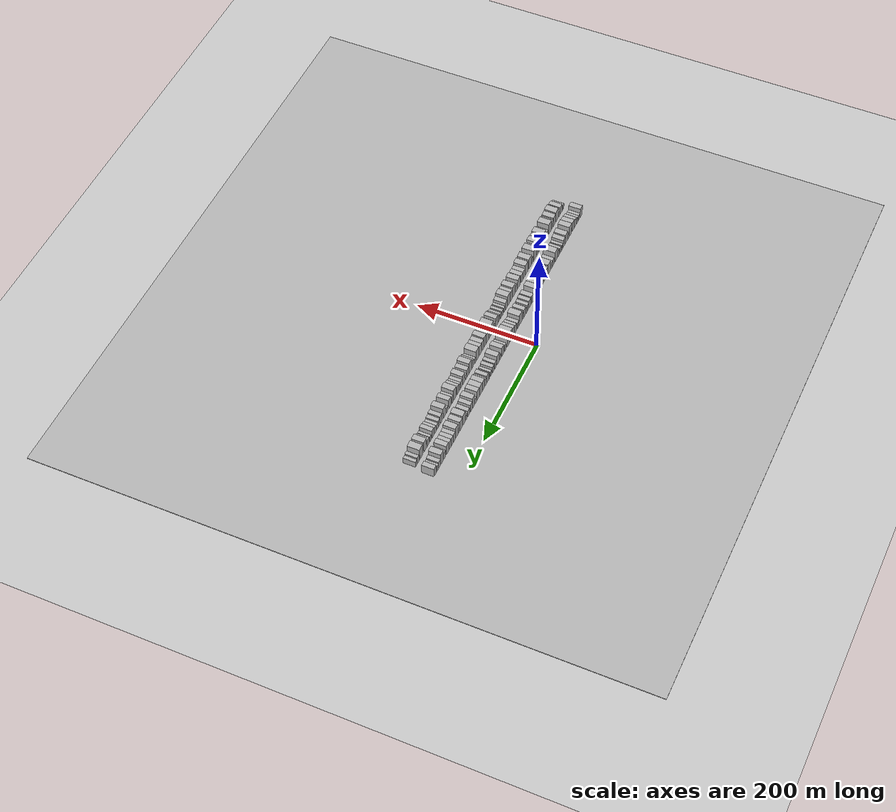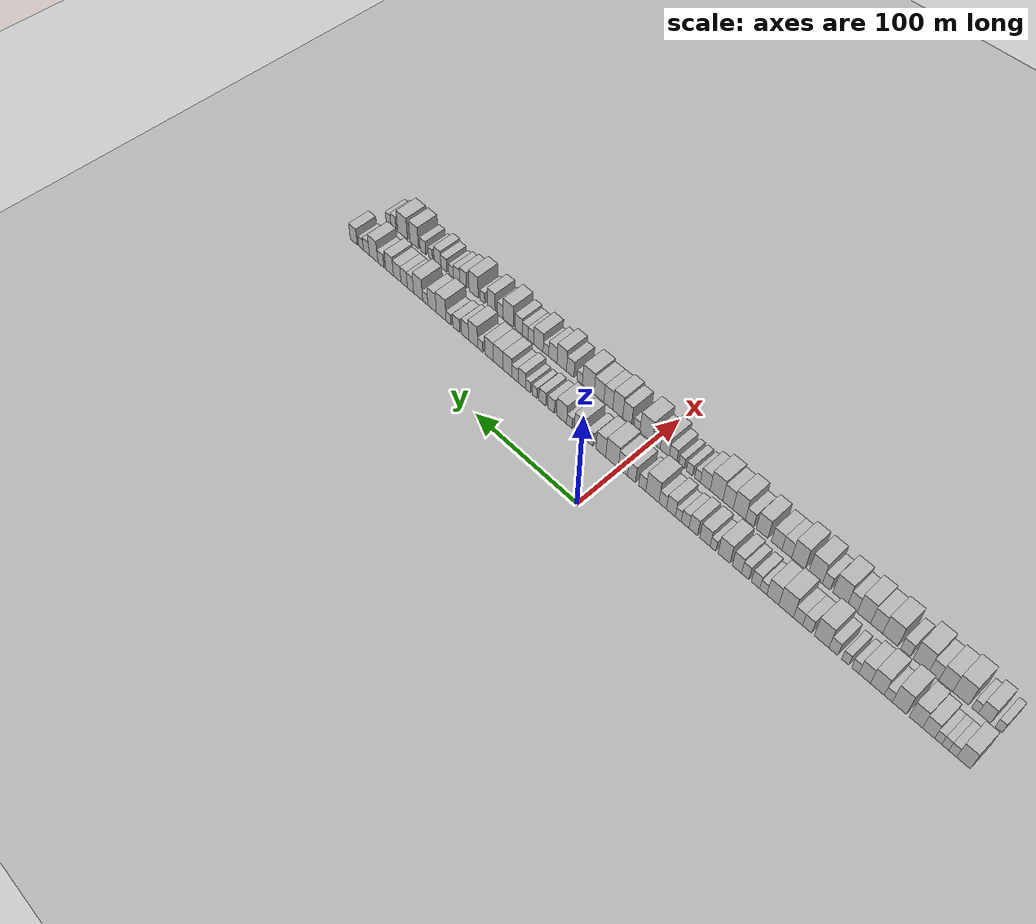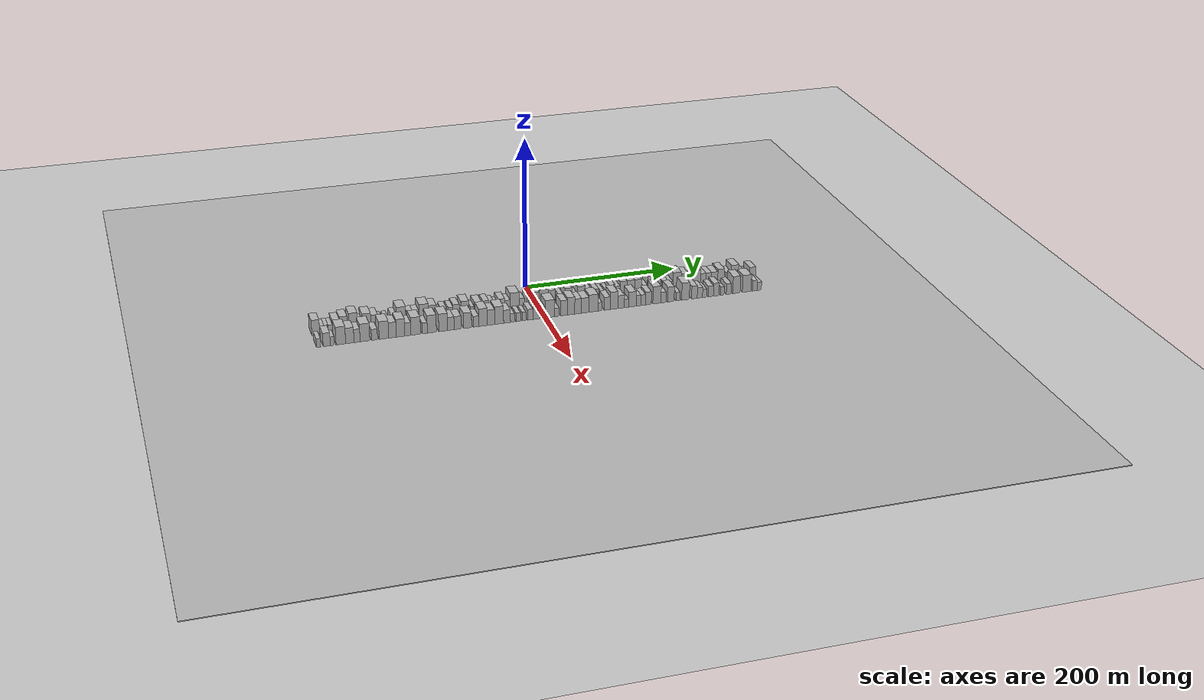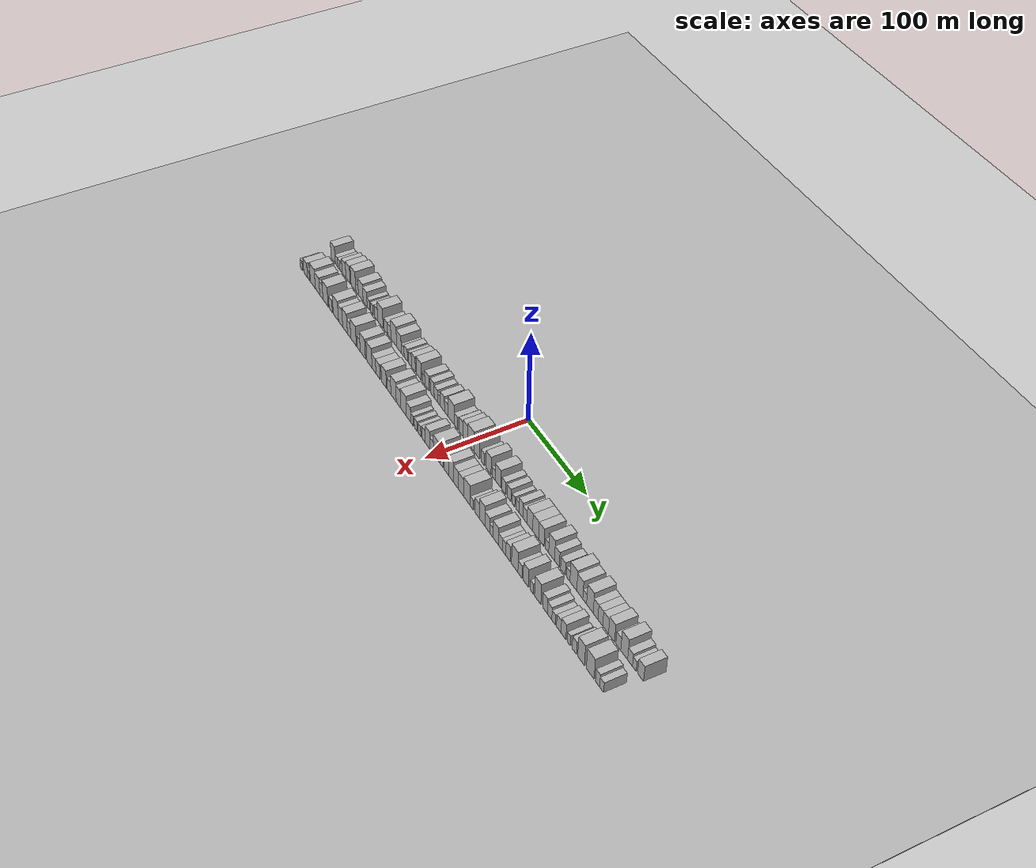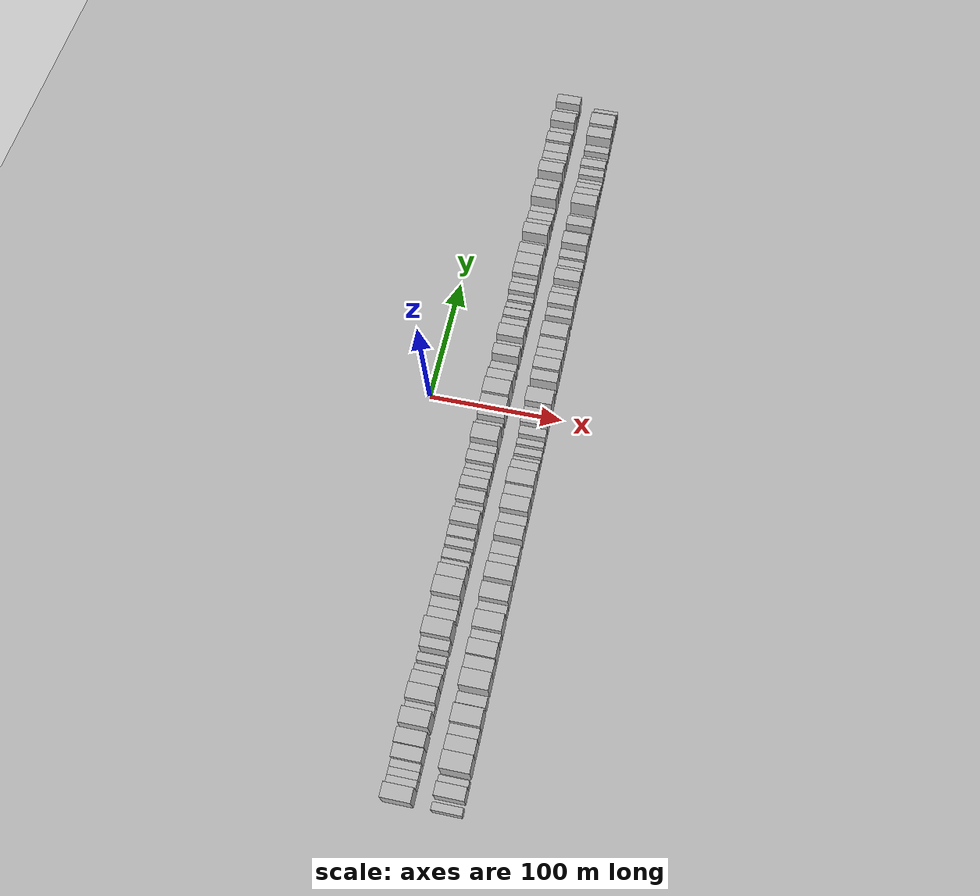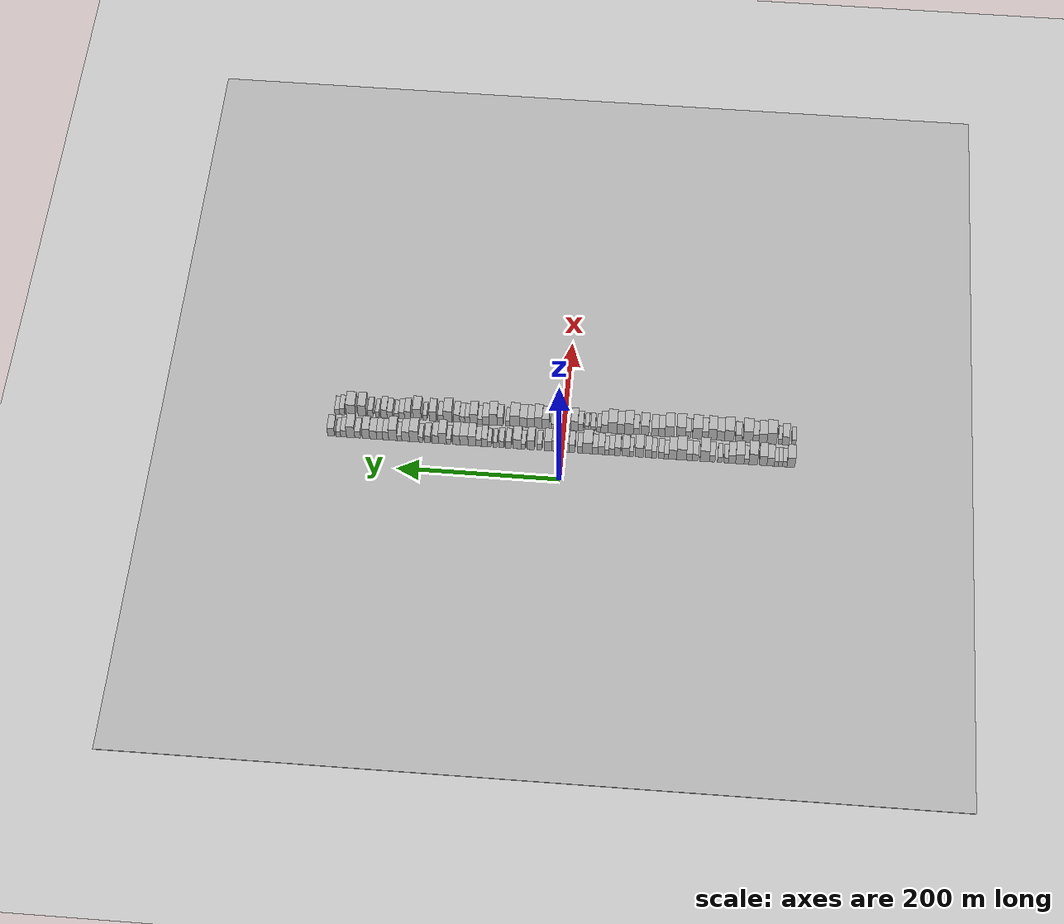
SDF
<?xml version="1.0" encoding="utf-8"?>

<sdf version="1.6">

   <world name="default">

      <gui fullscreen="0">

         <camera name="user_camera">

            <pose>-15 0 4.57585 0 0 0</pose>

            <view_controller>orbit</view_controller>

         </camera>

      </gui>

      <scene>

         <sky>

           <clouds>

             <speed>12</speed>

           </clouds>

         </sky>

         <ambient>0.4 0.4 0.4 1</ambient>

         <background>0.7 0.7 0.7 1</background>

         <shadows>1</shadows>

      </scene>

      <gravity>0 0 -9.8066</gravity>

      <magnetic_field>6e-06 2.3e-05 -4.2e-05</magnetic_field>

      <physics default="0" name="default_physics" type="ode">

         <ode>

            <solver>

               <type>quick</type>

               <iters>10</iters>

               <sor>1.0</sor>

               <use_dynamic_moi_rescaling>0</use_dynamic_moi_rescaling>

            </solver>

            <constraints>

               <cfm>0</cfm>

               <erp>0.2</erp>

               <contact_max_correcting_vel>100</contact_max_correcting_vel>

               <contact_surface_layer>0.001</contact_surface_layer>

            </constraints>

         </ode>

         <max_step_size>0.004</max_step_size>

         <real_time_factor>1</real_time_factor>

         <real_time_update_rate>250</real_time_update_rate>

      </physics>

      <light name="sun" type="directional">

         <cast_shadows>1</cast_shadows>

         <pose>0 0 10 0 0 0</pose>

         <diffuse>0.8 0.8 0.8 1</diffuse>

         <specular>0.2 0.2 0.2 1</specular>

         <attenuation>

            <range>1000</range>

            <constant>0.9</constant>

            <linear>0.01</linear>

            <quadratic>0.001</quadratic>

         </attenuation>

         <direction>-0.5 0.1 -0.9</direction>

      </light>

      <include>

         <name>ground_plane_1</name>

         <uri>model://HANNAS_ground_plane</uri>

         <pose>0 0 0  0 0 0</pose>

      </include>

      <include>

         <name>ground_plane_2</name>

         <uri>model://HANNAS_ground_plane</uri>

         <pose>100 0 0  0 0 0</pose>

      </include>

      <model name="building_1">

         <static>1</static>

         <pose frame="">50.0000 -279.2305 0 0.000000 0.000000 0.000000</pose>

         <link name="link">

            <pose frame="">0 0 10.50 0 0 0</pose>

            <collision name="collision">

               <geometry>

                  <box>

                     <size>20.0000 9.5390 21.0000</size>

                  </box>

               </geometry>

               <max_contacts>10</max_contacts>

               <surface>

                  <contact>

                     <ode/>

                  </contact>

                  <bounce/>

                  <friction>

                     <torsional>

                        <ode/>

                     </torsional>

                     <ode/>

                  </friction>

               </surface>

            </collision>

            <visual name="visual">

               <cast_shadows>0</cast_shadows>

               <geometry>

                  <box>

                     <size>20.0000 9.5390 21.0000</size>

                  </box>

               </geometry>

               <material>

                  <script>

                     <uri>model://HANNAS_wall/materials/scripts</uri>

                     <uri>model://HANNAS_wall/materials/textures</uri>

                     <name>vrc/HANNAS_wall</name>

                  </script>

               </material>

            </visual>

            <self_collide>0</self_collide>

            <enable_wind>0</enable_wind>

            <kinematic>0</kinematic>

         </link>

      </model>

      <model name="building_2">

         <static>1</static>

         <pose frame="">50.0000 -271.6400 0 0.000000 0.000000 0.000000</pose>

         <link name="link">

            <pose frame="">0 0 6.00 0 0 0</pose>

            <collision name="collision">

               <geometry>

                  <box>

                     <size>20.0000 5.6421 12.0000</size>

                  </box>

               </geometry>

               <max_contacts>10</max_contacts>

               <surface>

                  <contact>

                     <ode/>

                  </contact>

                  <bounce/>

                  <friction>

                     <torsional>

                        <ode/>

                     </torsional>

                     <ode/>

                  </friction>

               </surface>

            </collision>

            <visual name="visual">

               <cast_shadows>0</cast_shadows>

               <geometry>

                  <box>

                     <size>20.0000 5.6421 12.0000</size>

                  </box>

               </geometry>

               <material>

                  <script>

                     <uri>model://HANNAS_wall/materials/scripts</uri>

                     <uri>model://HANNAS_wall/materials/textures</uri>

                     <name>vrc/HANNAS_wall</name>

                  </script>

               </material>

            </visual>

            <self_collide>0</self_collide>

            <enable_wind>0</enable_wind>

            <kinematic>0</kinematic>

         </link>

      </model>

      <model name="building_3">

         <static>1</static>

         <pose frame="">50.0000 -266.3191 0 0.000000 0.000000 0.000000</pose>

         <link name="link">

            <pose frame="">0 0 6.00 0 0 0</pose>

            <collision name="collision">

               <geometry>

                  <box>

                     <size>20.0000 4.9997 12.0000</size>

                  </box>

               </geometry>

               <max_contacts>10</max_contacts>

               <surface>

                  <contact>

                     <ode/>

                  </contact>

                  <bounce/>

                  <friction>

                     <torsional>

                        <ode/>

                     </torsional>

                     <ode/>

                  </friction>

               </surface>

            </collision>

            <visual name="visual">

               <cast_shadows>0</cast_shadows>

               <geometry>

                  <box>

                     <size>20.0000 4.9997 12.0000</size>

                  </box>

               </geometry>

               <material>

                  <script>

                     <uri>model://HANNAS_wall/materials/scripts</uri>

                     <uri>model://HANNAS_wall/materials/textures</uri>

                     <name>vrc/HANNAS_wall</name>

                  </script>

               </material>

            </visual>

            <self_collide>0</self_collide>

            <enable_wind>0</enable_wind>

            <kinematic>0</kinematic>

         </link>

      </model>

      <model name="building_4">

         <static>1</static>

         <pose frame="">50.0000 -261.3050 0 0.000000 0.000000 0.000000</pose>

         <link name="link">

            <pose frame="">0 0 6.00 0 0 0</pose>

            <collision name="collision">

               <geometry>

                  <box>

                     <size>20.0000 5.0284 12.0000</size>

                  </box>

               </geometry>

               <max_contacts>10</max_contacts>

               <surface>

                  <contact>

                     <ode/>

                  </contact>

                  <bounce/>

                  <friction>

                     <torsional>

                        <ode/>

                     </torsional>

                     <ode/>

                  </friction>

               </surface>

            </collision>

            <visual name="visual">

               <cast_shadows>0</cast_shadows>

               <geometry>

                  <box>

                     <size>20.0000 5.0284 12.0000</size>

                  </box>

               </geometry>

               <material>

                  <script>

                     <uri>model://HANNAS_wall/materials/scripts</uri>

                     <uri>model://HANNAS_wall/materials/textures</uri>

                     <name>vrc/HANNAS_wall</name>

                  </script>

               </material>

            </visual>

            <self_collide>0</self_collide>

            <enable_wind>0</enable_wind>

            <kinematic>0</kinematic>

         </link>

      </model>

      <model name="building_5">

         <static>1</static>

         <pose frame="">50.0000 -254.3919 0 0.000000 0.000000 0.000000</pose>

         <link name="link">

            <pose frame="">0 0 9.00 0 0 0</pose>

            <collision name="collision">

               <geometry>

                  <box>

                     <size>20.0000 8.7978 18.0000</size>

                  </box>

               </geometry>

               <max_contacts>10</max_contacts>

               <surface>

                  <contact>

                     <ode/>

                  </contact>

                  <bounce/>

                  <friction>

                     <torsional>

                        <ode/>

                     </torsional>

                     <ode/>

                  </friction>

               </surface>

            </collision>

            <visual name="visual">

               <cast_shadows>0</cast_shadows>

               <geometry>

                  <box>

                     <size>20.0000 8.7978 18.0000</size>

                  </box>

               </geometry>

               <material>

                  <script>

                     <uri>model://HANNAS_wall/materials/scripts</uri>

                     <uri>model://HANNAS_wall/materials/textures</uri>

                     <name>vrc/HANNAS_wall</name>

                  </script>

               </material>

            </visual>

            <self_collide>0</self_collide>

            <enable_wind>0</enable_wind>

            <kinematic>0</kinematic>

         </link>

      </model>

      <model name="building_6">

         <static>1</static>

         <pose frame="">50.0000 -245.1955 0 0.000000 0.000000 0.000000</pose>

         <link name="link">

            <pose frame="">0 0 10.50 0 0 0</pose>

            <collision name="collision">

               <geometry>

                  <box>

                     <size>20.0000 9.5949 21.0000</size>

                  </box>

               </geometry>

               <max_contacts>10</max_contacts>

               <surface>

                  <contact>

                     <ode/>

                  </contact>

                  <bounce/>

                  <friction>

                     <torsional>

                        <ode/>

                     </torsional>

                     <ode/>

                  </friction>

               </surface>

            </collision>

            <visual name="visual">

               <cast_shadows>0</cast_shadows>

               <geometry>

                  <box>

                     <size>20.0000 9.5949 21.0000</size>

                  </box>

               </geometry>

               <material>

                  <script>

                     <uri>model://HANNAS_wall/materials/scripts</uri>

                     <uri>model://HANNAS_wall/materials/textures</uri>

                     <name>vrc/HANNAS_wall</name>

                  </script>

               </material>

            </visual>

            <self_collide>0</self_collide>

            <enable_wind>0</enable_wind>

            <kinematic>0</kinematic>

         </link>

      </model>

      <model name="building_7">

         <static>1</static>

         <pose frame="">50.0000 -233.1401 0 0.000000 0.000000 0.000000</pose>

         <link name="link">

            <pose frame="">0 0 12.00 0 0 0</pose>

            <collision name="collision">

               <geometry>

                  <box>

                     <size>20.0000 10.5159 24.0000</size>

                  </box>

               </geometry>

               <max_contacts>10</max_contacts>

               <surface>

                  <contact>

                     <ode/>

                  </contact>

                  <bounce/>

                  <friction>

                     <torsional>

                        <ode/>

                     </torsional>

                     <ode/>

                  </friction>

               </surface>

            </collision>

            <visual name="visual">

               <cast_shadows>0</cast_shadows>

               <geometry>

                  <box>

                     <size>20.0000 10.5159 24.0000</size>

                  </box>

               </geometry>

               <material>

                  <script>

                     <uri>model://HANNAS_wall/materials/scripts</uri>

                     <uri>model://HANNAS_wall/materials/textures</uri>

                     <name>vrc/HANNAS_wall</name>

                  </script>

               </material>

            </visual>

            <self_collide>0</self_collide>

            <enable_wind>0</enable_wind>

            <kinematic>0</kinematic>

         </link>

      </model>

      <model name="building_8">

         <static>1</static>

         <pose frame="">50.0000 -224.9332 0 0.000000 0.000000 0.000000</pose>

         <link name="link">

            <pose frame="">0 0 6.00 0 0 0</pose>

            <collision name="collision">

               <geometry>

                  <box>

                     <size>20.0000 5.8978 12.0000</size>

                  </box>

               </geometry>

               <max_contacts>10</max_contacts>

               <surface>

                  <contact>

                     <ode/>

                  </contact>

                  <bounce/>

                  <friction>

                     <torsional>

                        <ode/>

                     </torsional>

                     <ode/>

                  </friction>

               </surface>

            </collision>

            <visual name="visual">

               <cast_shadows>0</cast_shadows>

               <geometry>

                  <box>

                     <size>20.0000 5.8978 12.0000</size>

                  </box>

               </geometry>

               <material>

                  <script>

                     <uri>model://HANNAS_wall/materials/scripts</uri>

                     <uri>model://HANNAS_wall/materials/textures</uri>

                     <name>vrc/HANNAS_wall</name>

                  </script>

               </material>

            </visual>

            <self_collide>0</self_collide>

            <enable_wind>0</enable_wind>

            <kinematic>0</kinematic>

         </link>

      </model>

      <model name="building_9">

         <static>1</static>

         <pose frame="">50.0000 -216.7880 0 0.000000 0.000000 0.000000</pose>

         <link name="link">

            <pose frame="">0 0 10.50 0 0 0</pose>

            <collision name="collision">

               <geometry>

                  <box>

                     <size>20.0000 10.3926 21.0000</size>

                  </box>

               </geometry>

               <max_contacts>10</max_contacts>

               <surface>

                  <contact>

                     <ode/>

                  </contact>

                  <bounce/>

                  <friction>

                     <torsional>

                        <ode/>

                     </torsional>

                     <ode/>

                  </friction>

               </surface>

            </collision>

            <visual name="visual">

               <cast_shadows>0</cast_shadows>

               <geometry>

                  <box>

                     <size>20.0000 10.3926 21.0000</size>

                  </box>

               </geometry>

               <material>

                  <script>

                     <uri>model://HANNAS_wall/materials/scripts</uri>

                     <uri>model://HANNAS_wall/materials/textures</uri>

                     <name>vrc/HANNAS_wall</name>

                  </script>

               </material>

            </visual>

            <self_collide>0</self_collide>

            <enable_wind>0</enable_wind>

            <kinematic>0</kinematic>

         </link>

      </model>

      <model name="building_10">

         <static>1</static>

         <pose frame="">50.0000 -207.1930 0 0.000000 0.000000 0.000000</pose>

         <link name="link">

            <pose frame="">0 0 9.00 0 0 0</pose>

            <collision name="collision">

               <geometry>

                  <box>

                     <size>20.0000 8.7975 18.0000</size>

                  </box>

               </geometry>

               <max_contacts>10</max_contacts>

               <surface>

                  <contact>

                     <ode/>

                  </contact>

                  <bounce/>

                  <friction>

                     <torsional>

                        <ode/>

                     </torsional>

                     <ode/>

                  </friction>

               </surface>

            </collision>

            <visual name="visual">

               <cast_shadows>0</cast_shadows>

               <geometry>

                  <box>

                     <size>20.0000 8.7975 18.0000</size>

                  </box>

               </geometry>

               <material>

                  <script>

                     <uri>model://HANNAS_wall/materials/scripts</uri>

                     <uri>model://HANNAS_wall/materials/textures</uri>

                     <name>vrc/HANNAS_wall</name>

                  </script>

               </material>

            </visual>

            <self_collide>0</self_collide>

            <enable_wind>0</enable_wind>

            <kinematic>0</kinematic>

         </link>

      </model>

      <model name="building_11">

         <static>1</static>

         <pose frame="">50.0000 -200.0392 0 0.000000 0.000000 0.000000</pose>

         <link name="link">

            <pose frame="">0 0 6.00 0 0 0</pose>

            <collision name="collision">

               <geometry>

                  <box>

                     <size>20.0000 5.5100 12.0000</size>

                  </box>

               </geometry>

               <max_contacts>10</max_contacts>

               <surface>

                  <contact>

                     <ode/>

                  </contact>

                  <bounce/>

                  <friction>

                     <torsional>

                        <ode/>

                     </torsional>

                     <ode/>

                  </friction>

               </surface>

            </collision>

            <visual name="visual">

               <cast_shadows>0</cast_shadows>

               <geometry>

                  <box>

                     <size>20.0000 5.5100 12.0000</size>

                  </box>

               </geometry>

               <material>

                  <script>

                     <uri>model://HANNAS_wall/materials/scripts</uri>

                     <uri>model://HANNAS_wall/materials/textures</uri>

                     <name>vrc/HANNAS_wall</name>

                  </script>

               </material>

            </visual>

            <self_collide>0</self_collide>

            <enable_wind>0</enable_wind>

            <kinematic>0</kinematic>

         </link>

      </model>

      <model name="building_12">

         <static>1</static>

         <pose frame="">50.0000 -192.4610 0 0.000000 0.000000 0.000000</pose>

         <link name="link">

            <pose frame="">0 0 6.00 0 0 0</pose>

            <collision name="collision">

               <geometry>

                  <box>

                     <size>20.0000 5.6464 12.0000</size>

                  </box>

               </geometry>

               <max_contacts>10</max_contacts>

               <surface>

                  <contact>

                     <ode/>

                  </contact>

                  <bounce/>

                  <friction>

                     <torsional>

                        <ode/>

                     </torsional>

                     <ode/>

                  </friction>

               </surface>

            </collision>

            <visual name="visual">

               <cast_shadows>0</cast_shadows>

               <geometry>

                  <box>

                     <size>20.0000 5.6464 12.0000</size>

                  </box>

               </geometry>

               <material>

                  <script>

                     <uri>model://HANNAS_wall/materials/scripts</uri>

                     <uri>model://HANNAS_wall/materials/textures</uri>

                     <name>vrc/HANNAS_wall</name>

                  </script>

               </material>

            </visual>

            <self_collide>0</self_collide>

            <enable_wind>0</enable_wind>

            <kinematic>0</kinematic>

         </link>

      </model>

      <model name="building_13">

         <static>1</static>

         <pose frame="">50.0000 -183.1649 0 0.000000 0.000000 0.000000</pose>

         <link name="link">

            <pose frame="">0 0 7.50 0 0 0</pose>

            <collision name="collision">

               <geometry>

                  <box>

                     <size>20.0000 6.9459 15.0000</size>

                  </box>

               </geometry>

               <max_contacts>10</max_contacts>

               <surface>

                  <contact>

                     <ode/>

                  </contact>

                  <bounce/>

                  <friction>

                     <torsional>

                        <ode/>

                     </torsional>

                     <ode/>

                  </friction>

               </surface>

            </collision>

            <visual name="visual">

               <cast_shadows>0</cast_shadows>

               <geometry>

                  <box>

                     <size>20.0000 6.9459 15.0000</size>

                  </box>

               </geometry>

               <material>

                  <script>

                     <uri>model://HANNAS_wall/materials/scripts</uri>

                     <uri>model://HANNAS_wall/materials/textures</uri>

                     <name>vrc/HANNAS_wall</name>

                  </script>

               </material>

            </visual>

            <self_collide>0</self_collide>

            <enable_wind>0</enable_wind>

            <kinematic>0</kinematic>

         </link>

      </model>

      <model name="building_14">

         <static>1</static>

         <pose frame="">50.0000 -173.9697 0 0.000000 0.000000 0.000000</pose>

         <link name="link">

            <pose frame="">0 0 12.00 0 0 0</pose>

            <collision name="collision">

               <geometry>

                  <box>

                     <size>20.0000 11.4444 24.0000</size>

                  </box>

               </geometry>

               <max_contacts>10</max_contacts>

               <surface>

                  <contact>

                     <ode/>

                  </contact>

                  <bounce/>

                  <friction>

                     <torsional>

                        <ode/>

                     </torsional>

                     <ode/>

                  </friction>

               </surface>

            </collision>

            <visual name="visual">

               <cast_shadows>0</cast_shadows>

               <geometry>

                  <box>

                     <size>20.0000 11.4444 24.0000</size>

                  </box>

               </geometry>

               <material>

                  <script>

                     <uri>model://HANNAS_wall/materials/scripts</uri>

                     <uri>model://HANNAS_wall/materials/textures</uri>

                     <name>vrc/HANNAS_wall</name>

                  </script>

               </material>

            </visual>

            <self_collide>0</self_collide>

            <enable_wind>0</enable_wind>

            <kinematic>0</kinematic>

         </link>

      </model>

      <model name="building_15">

         <static>1</static>

         <pose frame="">50.0000 -162.5732 0 0.000000 0.000000 0.000000</pose>

         <link name="link">

            <pose frame="">0 0 7.50 0 0 0</pose>

            <collision name="collision">

               <geometry>

                  <box>

                     <size>20.0000 7.3485 15.0000</size>

                  </box>

               </geometry>

               <max_contacts>10</max_contacts>

               <surface>

                  <contact>

                     <ode/>

                  </contact>

                  <bounce/>

                  <friction>

                     <torsional>

                        <ode/>

                     </torsional>

                     <ode/>

                  </friction>

               </surface>

            </collision>

            <visual name="visual">

               <cast_shadows>0</cast_shadows>

               <geometry>

                  <box>

                     <size>20.0000 7.3485 15.0000</size>

                  </box>

               </geometry>

               <material>

                  <script>

                     <uri>model://HANNAS_wall/materials/scripts</uri>

                     <uri>model://HANNAS_wall/materials/textures</uri>

                     <name>vrc/HANNAS_wall</name>

                  </script>

               </material>

            </visual>

            <self_collide>0</self_collide>

            <enable_wind>0</enable_wind>

            <kinematic>0</kinematic>

         </link>

      </model>

      <model name="building_16">

         <static>1</static>

         <pose frame="">50.0000 -155.2108 0 0.000000 0.000000 0.000000</pose>

         <link name="link">

            <pose frame="">0 0 7.50 0 0 0</pose>

            <collision name="collision">

               <geometry>

                  <box>

                     <size>20.0000 7.3764 15.0000</size>

                  </box>

               </geometry>

               <max_contacts>10</max_contacts>

               <surface>

                  <contact>

                     <ode/>

                  </contact>

                  <bounce/>

                  <friction>

                     <torsional>

                        <ode/>

                     </torsional>

                     <ode/>

                  </friction>

               </surface>

            </collision>

            <visual name="visual">

               <cast_shadows>0</cast_shadows>

               <geometry>

                  <box>

                     <size>20.0000 7.3764 15.0000</size>

                  </box>

               </geometry>

               <material>

                  <script>

                     <uri>model://HANNAS_wall/materials/scripts</uri>

                     <uri>model://HANNAS_wall/materials/textures</uri>

                     <name>vrc/HANNAS_wall</name>

                  </script>

               </material>

            </visual>

            <self_collide>0</self_collide>

            <enable_wind>0</enable_wind>

            <kinematic>0</kinematic>

         </link>

      </model>

      <model name="building_17">

         <static>1</static>

         <pose frame="">50.0000 -145.5804 0 0.000000 0.000000 0.000000</pose>

         <link name="link">

            <pose frame="">0 0 12.00 0 0 0</pose>

            <collision name="collision">

               <geometry>

                  <box>

                     <size>20.0000 11.8843 24.0000</size>

                  </box>

               </geometry>

               <max_contacts>10</max_contacts>

               <surface>

                  <contact>

                     <ode/>

                  </contact>

                  <bounce/>

                  <friction>

                     <torsional>

                        <ode/>

                     </torsional>

                     <ode/>

                  </friction>

               </surface>

            </collision>

            <visual name="visual">

               <cast_shadows>0</cast_shadows>

               <geometry>

                  <box>

                     <size>20.0000 11.8843 24.0000</size>

                  </box>

               </geometry>

               <material>

                  <script>

                     <uri>model://HANNAS_wall/materials/scripts</uri>

                     <uri>model://HANNAS_wall/materials/textures</uri>

                     <name>vrc/HANNAS_wall</name>

                  </script>

               </material>

            </visual>

            <self_collide>0</self_collide>

            <enable_wind>0</enable_wind>

            <kinematic>0</kinematic>

         </link>

      </model>

      <model name="building_18">

         <static>1</static>

         <pose frame="">50.0000 -134.7544 0 0.000000 0.000000 0.000000</pose>

         <link name="link">

            <pose frame="">0 0 10.50 0 0 0</pose>

            <collision name="collision">

               <geometry>

                  <box>

                     <size>20.0000 9.7678 21.0000</size>

                  </box>

               </geometry>

               <max_contacts>10</max_contacts>

               <surface>

                  <contact>

                     <ode/>

                  </contact>

                  <bounce/>

                  <friction>

                     <torsional>

                        <ode/>

                     </torsional>

                     <ode/>

                  </friction>

               </surface>

            </collision>

            <visual name="visual">

               <cast_shadows>0</cast_shadows>

               <geometry>

                  <box>

                     <size>20.0000 9.7678 21.0000</size>

                  </box>

               </geometry>

               <material>

                  <script>

                     <uri>model://HANNAS_wall/materials/scripts</uri>

                     <uri>model://HANNAS_wall/materials/textures</uri>

                     <name>vrc/HANNAS_wall</name>

                  </script>

               </material>

            </visual>

            <self_collide>0</self_collide>

            <enable_wind>0</enable_wind>

            <kinematic>0</kinematic>

         </link>

      </model>

      <model name="building_19">

         <static>1</static>

         <pose frame="">50.0000 -126.9675 0 0.000000 0.000000 0.000000</pose>

         <link name="link">

            <pose frame="">0 0 6.00 0 0 0</pose>

            <collision name="collision">

               <geometry>

                  <box>

                     <size>20.0000 5.8060 12.0000</size>

                  </box>

               </geometry>

               <max_contacts>10</max_contacts>

               <surface>

                  <contact>

                     <ode/>

                  </contact>

                  <bounce/>

                  <friction>

                     <torsional>

                        <ode/>

                     </torsional>

                     <ode/>

                  </friction>

               </surface>

            </collision>

            <visual name="visual">

               <cast_shadows>0</cast_shadows>

               <geometry>

                  <box>

                     <size>20.0000 5.8060 12.0000</size>

                  </box>

               </geometry>

               <material>

                  <script>

                     <uri>model://HANNAS_wall/materials/scripts</uri>

                     <uri>model://HANNAS_wall/materials/textures</uri>

                     <name>vrc/HANNAS_wall</name>

                  </script>

               </material>

            </visual>

            <self_collide>0</self_collide>

            <enable_wind>0</enable_wind>

            <kinematic>0</kinematic>

         </link>

      </model>

      <model name="building_20">

         <static>1</static>

         <pose frame="">50.0000 -120.5750 0 0.000000 0.000000 0.000000</pose>

         <link name="link">

            <pose frame="">0 0 7.50 0 0 0</pose>

            <collision name="collision">

               <geometry>

                  <box>

                     <size>20.0000 6.9789 15.0000</size>

                  </box>

               </geometry>

               <max_contacts>10</max_contacts>

               <surface>

                  <contact>

                     <ode/>

                  </contact>

                  <bounce/>

                  <friction>

                     <torsional>

                        <ode/>

                     </torsional>

                     <ode/>

                  </friction>

               </surface>

            </collision>

            <visual name="visual">

               <cast_shadows>0</cast_shadows>

               <geometry>

                  <box>

                     <size>20.0000 6.9789 15.0000</size>

                  </box>

               </geometry>

               <material>

                  <script>

                     <uri>model://HANNAS_wall/materials/scripts</uri>

                     <uri>model://HANNAS_wall/materials/textures</uri>

                     <name>vrc/HANNAS_wall</name>

                  </script>

               </material>

            </visual>

            <self_collide>0</self_collide>

            <enable_wind>0</enable_wind>

            <kinematic>0</kinematic>

         </link>

      </model>

      <model name="building_21">

         <static>1</static>

         <pose frame="">50.0000 -112.0053 0 0.000000 0.000000 0.000000</pose>

         <link name="link">

            <pose frame="">0 0 7.50 0 0 0</pose>

            <collision name="collision">

               <geometry>

                  <box>

                     <size>20.0000 6.1606 15.0000</size>

                  </box>

               </geometry>

               <max_contacts>10</max_contacts>

               <surface>

                  <contact>

                     <ode/>

                  </contact>

                  <bounce/>

                  <friction>

                     <torsional>

                        <ode/>

                     </torsional>

                     <ode/>

                  </friction>

               </surface>

            </collision>

            <visual name="visual">

               <cast_shadows>0</cast_shadows>

               <geometry>

                  <box>

                     <size>20.0000 6.1606 15.0000</size>

                  </box>

               </geometry>

               <material>

                  <script>

                     <uri>model://HANNAS_wall/materials/scripts</uri>

                     <uri>model://HANNAS_wall/materials/textures</uri>

                     <name>vrc/HANNAS_wall</name>

                  </script>

               </material>

            </visual>

            <self_collide>0</self_collide>

            <enable_wind>0</enable_wind>

            <kinematic>0</kinematic>

         </link>

      </model>

      <model name="building_22">

         <static>1</static>

         <pose frame="">50.0000 -104.9959 0 0.000000 0.000000 0.000000</pose>

         <link name="link">

            <pose frame="">0 0 9.00 0 0 0</pose>

            <collision name="collision">

               <geometry>

                  <box>

                     <size>20.0000 7.8580 18.0000</size>

                  </box>

               </geometry>

               <max_contacts>10</max_contacts>

               <surface>

                  <contact>

                     <ode/>

                  </contact>

                  <bounce/>

                  <friction>

                     <torsional>

                        <ode/>

                     </torsional>

                     <ode/>

                  </friction>

               </surface>

            </collision>

            <visual name="visual">

               <cast_shadows>0</cast_shadows>

               <geometry>

                  <box>

                     <size>20.0000 7.8580 18.0000</size>

                  </box>

               </geometry>

               <material>

                  <script>

                     <uri>model://HANNAS_wall/materials/scripts</uri>

                     <uri>model://HANNAS_wall/materials/textures</uri>

                     <name>vrc/HANNAS_wall</name>

                  </script>

               </material>

            </visual>

            <self_collide>0</self_collide>

            <enable_wind>0</enable_wind>

            <kinematic>0</kinematic>

         </link>

      </model>

      <model name="building_23">

         <static>1</static>

         <pose frame="">50.0000 -93.9681 0 0.000000 0.000000 0.000000</pose>

         <link name="link">

            <pose frame="">0 0 10.50 0 0 0</pose>

            <collision name="collision">

               <geometry>

                  <box>

                     <size>20.0000 10.1976 21.0000</size>

                  </box>

               </geometry>

               <max_contacts>10</max_contacts>

               <surface>

                  <contact>

                     <ode/>

                  </contact>

                  <bounce/>

                  <friction>

                     <torsional>

                        <ode/>

                     </torsional>

                     <ode/>

                  </friction>

               </surface>

            </collision>

            <visual name="visual">

               <cast_shadows>0</cast_shadows>

               <geometry>

                  <box>

                     <size>20.0000 10.1976 21.0000</size>

                  </box>

               </geometry>

               <material>

                  <script>

                     <uri>model://HANNAS_wall/materials/scripts</uri>

                     <uri>model://HANNAS_wall/materials/textures</uri>

                     <name>vrc/HANNAS_wall</name>

                  </script>

               </material>

            </visual>

            <self_collide>0</self_collide>

            <enable_wind>0</enable_wind>

            <kinematic>0</kinematic>

         </link>

      </model>

      <model name="building_24">

         <static>1</static>

         <pose frame="">50.0000 -84.4433 0 0.000000 0.000000 0.000000</pose>

         <link name="link">

            <pose frame="">0 0 6.00 0 0 0</pose>

            <collision name="collision">

               <geometry>

                  <box>

                     <size>20.0000 4.8520 12.0000</size>

                  </box>

               </geometry>

               <max_contacts>10</max_contacts>

               <surface>

                  <contact>

                     <ode/>

                  </contact>

                  <bounce/>

                  <friction>

                     <torsional>

                        <ode/>

                     </torsional>

                     <ode/>

                  </friction>

               </surface>

            </collision>

            <visual name="visual">

               <cast_shadows>0</cast_shadows>

               <geometry>

                  <box>

                     <size>20.0000 4.8520 12.0000</size>

                  </box>

               </geometry>

               <material>

                  <script>

                     <uri>model://HANNAS_wall/materials/scripts</uri>

                     <uri>model://HANNAS_wall/materials/textures</uri>

                     <name>vrc/HANNAS_wall</name>

                  </script>

               </material>

            </visual>

            <self_collide>0</self_collide>

            <enable_wind>0</enable_wind>

            <kinematic>0</kinematic>

         </link>

      </model>

      <model name="building_25">

         <static>1</static>

         <pose frame="">50.0000 -77.5244 0 0.000000 0.000000 0.000000</pose>

         <link name="link">

            <pose frame="">0 0 9.00 0 0 0</pose>

            <collision name="collision">

               <geometry>

                  <box>

                     <size>20.0000 8.9857 18.0000</size>

                  </box>

               </geometry>

               <max_contacts>10</max_contacts>

               <surface>

                  <contact>

                     <ode/>

                  </contact>

                  <bounce/>

                  <friction>

                     <torsional>

                        <ode/>

                     </torsional>

                     <ode/>

                  </friction>

               </surface>

            </collision>

            <visual name="visual">

               <cast_shadows>0</cast_shadows>

               <geometry>

                  <box>

                     <size>20.0000 8.9857 18.0000</size>

                  </box>

               </geometry>

               <material>

                  <script>

                     <uri>model://HANNAS_wall/materials/scripts</uri>

                     <uri>model://HANNAS_wall/materials/textures</uri>

                     <name>vrc/HANNAS_wall</name>

                  </script>

               </material>

            </visual>

            <self_collide>0</self_collide>

            <enable_wind>0</enable_wind>

            <kinematic>0</kinematic>

         </link>

      </model>

      <model name="building_26">

         <static>1</static>

         <pose frame="">50.0000 -67.2787 0 0.000000 0.000000 0.000000</pose>

         <link name="link">

            <pose frame="">0 0 9.00 0 0 0</pose>

            <collision name="collision">

               <geometry>

                  <box>

                     <size>20.0000 7.5058 18.0000</size>

                  </box>

               </geometry>

               <max_contacts>10</max_contacts>

               <surface>

                  <contact>

                     <ode/>

                  </contact>

                  <bounce/>

                  <friction>

                     <torsional>

                        <ode/>

                     </torsional>

                     <ode/>

                  </friction>

               </surface>

            </collision>

            <visual name="visual">

               <cast_shadows>0</cast_shadows>

               <geometry>

                  <box>

                     <size>20.0000 7.5058 18.0000</size>

                  </box>

               </geometry>

               <material>

                  <script>

                     <uri>model://HANNAS_wall/materials/scripts</uri>

                     <uri>model://HANNAS_wall/materials/textures</uri>

                     <name>vrc/HANNAS_wall</name>

                  </script>

               </material>

            </visual>

            <self_collide>0</self_collide>

            <enable_wind>0</enable_wind>

            <kinematic>0</kinematic>

         </link>

      </model>

      <model name="building_27">

         <static>1</static>

         <pose frame="">50.0000 -60.1439 0 0.000000 0.000000 0.000000</pose>

         <link name="link">

            <pose frame="">0 0 7.50 0 0 0</pose>

            <collision name="collision">

               <geometry>

                  <box>

                     <size>20.0000 6.7638 15.0000</size>

                  </box>

               </geometry>

               <max_contacts>10</max_contacts>

               <surface>

                  <contact>

                     <ode/>

                  </contact>

                  <bounce/>

                  <friction>

                     <torsional>

                        <ode/>

                     </torsional>

                     <ode/>

                  </friction>

               </surface>

            </collision>

            <visual name="visual">

               <cast_shadows>0</cast_shadows>

               <geometry>

                  <box>

                     <size>20.0000 6.7638 15.0000</size>

                  </box>

               </geometry>

               <material>

                  <script>

                     <uri>model://HANNAS_wall/materials/scripts</uri>

                     <uri>model://HANNAS_wall/materials/textures</uri>

                     <name>vrc/HANNAS_wall</name>

                  </script>

               </material>

            </visual>

            <self_collide>0</self_collide>

            <enable_wind>0</enable_wind>

            <kinematic>0</kinematic>

         </link>

      </model>

      <model name="building_28">

         <static>1</static>

         <pose frame="">50.0000 -54.0815 0 0.000000 0.000000 0.000000</pose>

         <link name="link">

            <pose frame="">0 0 6.00 0 0 0</pose>

            <collision name="collision">

               <geometry>

                  <box>

                     <size>20.0000 5.3612 12.0000</size>

                  </box>

               </geometry>

               <max_contacts>10</max_contacts>

               <surface>

                  <contact>

                     <ode/>

                  </contact>

                  <bounce/>

                  <friction>

                     <torsional>

                        <ode/>

                     </torsional>

                     <ode/>

                  </friction>

               </surface>

            </collision>

            <visual name="visual">

               <cast_shadows>0</cast_shadows>

               <geometry>

                  <box>

                     <size>20.0000 5.3612 12.0000</size>

                  </box>

               </geometry>

               <material>

                  <script>

                     <uri>model://HANNAS_wall/materials/scripts</uri>

                     <uri>model://HANNAS_wall/materials/textures</uri>

                     <name>vrc/HANNAS_wall</name>

                  </script>

               </material>

            </visual>

            <self_collide>0</self_collide>

            <enable_wind>0</enable_wind>

            <kinematic>0</kinematic>

         </link>

      </model>

      <model name="building_29">

         <static>1</static>

         <pose frame="">50.0000 -47.3801 0 0.000000 0.000000 0.000000</pose>

         <link name="link">

            <pose frame="">0 0 9.00 0 0 0</pose>

            <collision name="collision">

               <geometry>

                  <box>

                     <size>20.0000 8.0416 18.0000</size>

                  </box>

               </geometry>

               <max_contacts>10</max_contacts>

               <surface>

                  <contact>

                     <ode/>

                  </contact>

                  <bounce/>

                  <friction>

                     <torsional>

                        <ode/>

                     </torsional>

                     <ode/>

                  </friction>

               </surface>

            </collision>

            <visual name="visual">

               <cast_shadows>0</cast_shadows>

               <geometry>

                  <box>

                     <size>20.0000 8.0416 18.0000</size>

                  </box>

               </geometry>

               <material>

                  <script>

                     <uri>model://HANNAS_wall/materials/scripts</uri>

                     <uri>model://HANNAS_wall/materials/textures</uri>

                     <name>vrc/HANNAS_wall</name>

                  </script>

               </material>

            </visual>

            <self_collide>0</self_collide>

            <enable_wind>0</enable_wind>

            <kinematic>0</kinematic>

         </link>

      </model>

      <model name="building_30">

         <static>1</static>

         <pose frame="">50.0000 -39.9776 0 0.000000 0.000000 0.000000</pose>

         <link name="link">

            <pose frame="">0 0 7.50 0 0 0</pose>

            <collision name="collision">

               <geometry>

                  <box>

                     <size>20.0000 6.7633 15.0000</size>

                  </box>

               </geometry>

               <max_contacts>10</max_contacts>

               <surface>

                  <contact>

                     <ode/>

                  </contact>

                  <bounce/>

                  <friction>

                     <torsional>

                        <ode/>

                     </torsional>

                     <ode/>

                  </friction>

               </surface>

            </collision>

            <visual name="visual">

               <cast_shadows>0</cast_shadows>

               <geometry>

                  <box>

                     <size>20.0000 6.7633 15.0000</size>

                  </box>

               </geometry>

               <material>

                  <script>

                     <uri>model://HANNAS_wall/materials/scripts</uri>

                     <uri>model://HANNAS_wall/materials/textures</uri>

                     <name>vrc/HANNAS_wall</name>

                  </script>

               </material>

            </visual>

            <self_collide>0</self_collide>

            <enable_wind>0</enable_wind>

            <kinematic>0</kinematic>

         </link>

      </model>

      <model name="building_31">

         <static>1</static>

         <pose frame="">50.0000 -30.6100 0 0.000000 0.000000 0.000000</pose>

         <link name="link">

            <pose frame="">0 0 12.00 0 0 0</pose>

            <collision name="collision">

               <geometry>

                  <box>

                     <size>20.0000 11.9720 24.0000</size>

                  </box>

               </geometry>

               <max_contacts>10</max_contacts>

               <surface>

                  <contact>

                     <ode/>

                  </contact>

                  <bounce/>

                  <friction>

                     <torsional>

                        <ode/>

                     </torsional>

                     <ode/>

                  </friction>

               </surface>

            </collision>

            <visual name="visual">

               <cast_shadows>0</cast_shadows>

               <geometry>

                  <box>

                     <size>20.0000 11.9720 24.0000</size>

                  </box>

               </geometry>

               <material>

                  <script>

                     <uri>model://HANNAS_wall/materials/scripts</uri>

                     <uri>model://HANNAS_wall/materials/textures</uri>

                     <name>vrc/HANNAS_wall</name>

                  </script>

               </material>

            </visual>

            <self_collide>0</self_collide>

            <enable_wind>0</enable_wind>

            <kinematic>0</kinematic>

         </link>

      </model>

      <model name="building_32">

         <static>1</static>

         <pose frame="">50.0000 -21.3559 0 0.000000 0.000000 0.000000</pose>

         <link name="link">

            <pose frame="">0 0 7.50 0 0 0</pose>

            <collision name="collision">

               <geometry>

                  <box>

                     <size>20.0000 6.5360 15.0000</size>

                  </box>

               </geometry>

               <max_contacts>10</max_contacts>

               <surface>

                  <contact>

                     <ode/>

                  </contact>

                  <bounce/>

                  <friction>

                     <torsional>

                        <ode/>

                     </torsional>

                     <ode/>

                  </friction>

               </surface>

            </collision>

            <visual name="visual">

               <cast_shadows>0</cast_shadows>

               <geometry>

                  <box>

                     <size>20.0000 6.5360 15.0000</size>

                  </box>

               </geometry>

               <material>

                  <script>

                     <uri>model://HANNAS_wall/materials/scripts</uri>

                     <uri>model://HANNAS_wall/materials/textures</uri>

                     <name>vrc/HANNAS_wall</name>

                  </script>

               </material>

            </visual>

            <self_collide>0</self_collide>

            <enable_wind>0</enable_wind>

            <kinematic>0</kinematic>

         </link>

      </model>

      <model name="building_33">

         <static>1</static>

         <pose frame="">50.0000 -11.3992 0 0.000000 0.000000 0.000000</pose>

         <link name="link">

            <pose frame="">0 0 9.00 0 0 0</pose>

            <collision name="collision">

               <geometry>

                  <box>

                     <size>20.0000 7.3775 18.0000</size>

                  </box>

               </geometry>

               <max_contacts>10</max_contacts>

               <surface>

                  <contact>

                     <ode/>

                  </contact>

                  <bounce/>

                  <friction>

                     <torsional>

                        <ode/>

                     </torsional>

                     <ode/>

                  </friction>

               </surface>

            </collision>

            <visual name="visual">

               <cast_shadows>0</cast_shadows>

               <geometry>

                  <box>

                     <size>20.0000 7.3775 18.0000</size>

                  </box>

               </geometry>

               <material>

                  <script>

                     <uri>model://HANNAS_wall/materials/scripts</uri>

                     <uri>model://HANNAS_wall/materials/textures</uri>

                     <name>vrc/HANNAS_wall</name>

                  </script>

               </material>

            </visual>

            <self_collide>0</self_collide>

            <enable_wind>0</enable_wind>

            <kinematic>0</kinematic>

         </link>

      </model>

      <model name="building_34">

         <static>1</static>

         <pose frame="">50.0000 -3.3811 0 0.000000 0.000000 0.000000</pose>

         <link name="link">

            <pose frame="">0 0 10.50 0 0 0</pose>

            <collision name="collision">

               <geometry>

                  <box>

                     <size>20.0000 8.6587 21.0000</size>

                  </box>

               </geometry>

               <max_contacts>10</max_contacts>

               <surface>

                  <contact>

                     <ode/>

                  </contact>

                  <bounce/>

                  <friction>

                     <torsional>

                        <ode/>

                     </torsional>

                     <ode/>

                  </friction>

               </surface>

            </collision>

            <visual name="visual">

               <cast_shadows>0</cast_shadows>

               <geometry>

                  <box>

                     <size>20.0000 8.6587 21.0000</size>

                  </box>

               </geometry>

               <material>

                  <script>

                     <uri>model://HANNAS_wall/materials/scripts</uri>

                     <uri>model://HANNAS_wall/materials/textures</uri>

                     <name>vrc/HANNAS_wall</name>

                  </script>

               </material>

            </visual>

            <self_collide>0</self_collide>

            <enable_wind>0</enable_wind>

            <kinematic>0</kinematic>

         </link>

      </model>

      <model name="building_35">

         <static>1</static>

         <pose frame="">50.0000 6.9286 0 0.000000 0.000000 0.000000</pose>

         <link name="link">

            <pose frame="">0 0 12.00 0 0 0</pose>

            <collision name="collision">

               <geometry>

                  <box>

                     <size>20.0000 11.9607 24.0000</size>

                  </box>

               </geometry>

               <max_contacts>10</max_contacts>

               <surface>

                  <contact>

                     <ode/>

                  </contact>

                  <bounce/>

                  <friction>

                     <torsional>

                        <ode/>

                     </torsional>

                     <ode/>

                  </friction>

               </surface>

            </collision>

            <visual name="visual">

               <cast_shadows>0</cast_shadows>

               <geometry>

                  <box>

                     <size>20.0000 11.9607 24.0000</size>

                  </box>

               </geometry>

               <material>

                  <script>

                     <uri>model://HANNAS_wall/materials/scripts</uri>

                     <uri>model://HANNAS_wall/materials/textures</uri>

                     <name>vrc/HANNAS_wall</name>

                  </script>

               </material>

            </visual>

            <self_collide>0</self_collide>

            <enable_wind>0</enable_wind>

            <kinematic>0</kinematic>

         </link>

      </model>

      <model name="building_36">

         <static>1</static>

         <pose frame="">50.0000 17.5560 0 0.000000 0.000000 0.000000</pose>

         <link name="link">

            <pose frame="">0 0 10.50 0 0 0</pose>

            <collision name="collision">

               <geometry>

                  <box>

                     <size>20.0000 9.2942 21.0000</size>

                  </box>

               </geometry>

               <max_contacts>10</max_contacts>

               <surface>

                  <contact>

                     <ode/>

                  </contact>

                  <bounce/>

                  <friction>

                     <torsional>

                        <ode/>

                     </torsional>

                     <ode/>

                  </friction>

               </surface>

            </collision>

            <visual name="visual">

               <cast_shadows>0</cast_shadows>

               <geometry>

                  <box>

                     <size>20.0000 9.2942 21.0000</size>

                  </box>

               </geometry>

               <material>

                  <script>

                     <uri>model://HANNAS_wall/materials/scripts</uri>

                     <uri>model://HANNAS_wall/materials/textures</uri>

                     <name>vrc/HANNAS_wall</name>

                  </script>

               </material>

            </visual>

            <self_collide>0</self_collide>

            <enable_wind>0</enable_wind>

            <kinematic>0</kinematic>

         </link>

      </model>

      <model name="building_37">

         <static>1</static>

         <pose frame="">50.0000 28.2883 0 0.000000 0.000000 0.000000</pose>

         <link name="link">

            <pose frame="">0 0 7.50 0 0 0</pose>

            <collision name="collision">

               <geometry>

                  <box>

                     <size>20.0000 6.1704 15.0000</size>

                  </box>

               </geometry>

               <max_contacts>10</max_contacts>

               <surface>

                  <contact>

                     <ode/>

                  </contact>

                  <bounce/>

                  <friction>

                     <torsional>

                        <ode/>

                     </torsional>

                     <ode/>

                  </friction>

               </surface>

            </collision>

            <visual name="visual">

               <cast_shadows>0</cast_shadows>

               <geometry>

                  <box>

                     <size>20.0000 6.1704 15.0000</size>

                  </box>

               </geometry>

               <material>

                  <script>

                     <uri>model://HANNAS_wall/materials/scripts</uri>

                     <uri>model://HANNAS_wall/materials/textures</uri>

                     <name>vrc/HANNAS_wall</name>

                  </script>

               </material>

            </visual>

            <self_collide>0</self_collide>

            <enable_wind>0</enable_wind>

            <kinematic>0</kinematic>

         </link>

      </model>

      <model name="building_38">

         <static>1</static>

         <pose frame="">50.0000 38.9013 0 0.000000 0.000000 0.000000</pose>

         <link name="link">

            <pose frame="">0 0 10.50 0 0 0</pose>

            <collision name="collision">

               <geometry>

                  <box>

                     <size>20.0000 9.0557 21.0000</size>

                  </box>

               </geometry>

               <max_contacts>10</max_contacts>

               <surface>

                  <contact>

                     <ode/>

                  </contact>

                  <bounce/>

                  <friction>

                     <torsional>

                        <ode/>

                     </torsional>

                     <ode/>

                  </friction>

               </surface>

            </collision>

            <visual name="visual">

               <cast_shadows>0</cast_shadows>

               <geometry>

                  <box>

                     <size>20.0000 9.0557 21.0000</size>

                  </box>

               </geometry>

               <material>

                  <script>

                     <uri>model://HANNAS_wall/materials/scripts</uri>

                     <uri>model://HANNAS_wall/materials/textures</uri>

                     <name>vrc/HANNAS_wall</name>

                  </script>

               </material>

            </visual>

            <self_collide>0</self_collide>

            <enable_wind>0</enable_wind>

            <kinematic>0</kinematic>

         </link>

      </model>

      <model name="building_39">

         <static>1</static>

         <pose frame="">50.0000 48.1322 0 0.000000 0.000000 0.000000</pose>

         <link name="link">

            <pose frame="">0 0 6.00 0 0 0</pose>

            <collision name="collision">

               <geometry>

                  <box>

                     <size>20.0000 5.4062 12.0000</size>

                  </box>

               </geometry>

               <max_contacts>10</max_contacts>

               <surface>

                  <contact>

                     <ode/>

                  </contact>

                  <bounce/>

                  <friction>

                     <torsional>

                        <ode/>

                     </torsional>

                     <ode/>

                  </friction>

               </surface>

            </collision>

            <visual name="visual">

               <cast_shadows>0</cast_shadows>

               <geometry>

                  <box>

                     <size>20.0000 5.4062 12.0000</size>

                  </box>

               </geometry>

               <material>

                  <script>

                     <uri>model://HANNAS_wall/materials/scripts</uri>

                     <uri>model://HANNAS_wall/materials/textures</uri>

                     <name>vrc/HANNAS_wall</name>

                  </script>

               </material>

            </visual>

            <self_collide>0</self_collide>

            <enable_wind>0</enable_wind>

            <kinematic>0</kinematic>

         </link>

      </model>

      <model name="building_40">

         <static>1</static>

         <pose frame="">50.0000 55.9080 0 0.000000 0.000000 0.000000</pose>

         <link name="link">

            <pose frame="">0 0 10.50 0 0 0</pose>

            <collision name="collision">

               <geometry>

                  <box>

                     <size>20.0000 10.1454 21.0000</size>

                  </box>

               </geometry>

               <max_contacts>10</max_contacts>

               <surface>

                  <contact>

                     <ode/>

                  </contact>

                  <bounce/>

                  <friction>

                     <torsional>

                        <ode/>

                     </torsional>

                     <ode/>

                  </friction>

               </surface>

            </collision>

            <visual name="visual">

               <cast_shadows>0</cast_shadows>

               <geometry>

                  <box>

                     <size>20.0000 10.1454 21.0000</size>

                  </box>

               </geometry>

               <material>

                  <script>

                     <uri>model://HANNAS_wall/materials/scripts</uri>

                     <uri>model://HANNAS_wall/materials/textures</uri>

                     <name>vrc/HANNAS_wall</name>

                  </script>

               </material>

            </visual>

            <self_collide>0</self_collide>

            <enable_wind>0</enable_wind>

            <kinematic>0</kinematic>

         </link>

      </model>

      <model name="building_41">

         <static>1</static>

         <pose frame="">50.0000 66.3840 0 0.000000 0.000000 0.000000</pose>

         <link name="link">

            <pose frame="">0 0 7.50 0 0 0</pose>

            <collision name="collision">

               <geometry>

                  <box>

                     <size>20.0000 6.8065 15.0000</size>

                  </box>

               </geometry>

               <max_contacts>10</max_contacts>

               <surface>

                  <contact>

                     <ode/>

                  </contact>

                  <bounce/>

                  <friction>

                     <torsional>

                        <ode/>

                     </torsional>

                     <ode/>

                  </friction>

               </surface>

            </collision>

            <visual name="visual">

               <cast_shadows>0</cast_shadows>

               <geometry>

                  <box>

                     <size>20.0000 6.8065 15.0000</size>

                  </box>

               </geometry>

               <material>

                  <script>

                     <uri>model://HANNAS_wall/materials/scripts</uri>

                     <uri>model://HANNAS_wall/materials/textures</uri>

                     <name>vrc/HANNAS_wall</name>

                  </script>

               </material>

            </visual>

            <self_collide>0</self_collide>

            <enable_wind>0</enable_wind>

            <kinematic>0</kinematic>

         </link>

      </model>

      <model name="building_42">

         <static>1</static>

         <pose frame="">50.0000 75.1720 0 0.000000 0.000000 0.000000</pose>

         <link name="link">

            <pose frame="">0 0 7.50 0 0 0</pose>

            <collision name="collision">

               <geometry>

                  <box>

                     <size>20.0000 6.7694 15.0000</size>

                  </box>

               </geometry>

               <max_contacts>10</max_contacts>

               <surface>

                  <contact>

                     <ode/>

                  </contact>

                  <bounce/>

                  <friction>

                     <torsional>

                        <ode/>

                     </torsional>

                     <ode/>

                  </friction>

               </surface>

            </collision>

            <visual name="visual">

               <cast_shadows>0</cast_shadows>

               <geometry>

                  <box>

                     <size>20.0000 6.7694 15.0000</size>

                  </box>

               </geometry>

               <material>

                  <script>

                     <uri>model://HANNAS_wall/materials/scripts</uri>

                     <uri>model://HANNAS_wall/materials/textures</uri>

                     <name>vrc/HANNAS_wall</name>

                  </script>

               </material>

            </visual>

            <self_collide>0</self_collide>

            <enable_wind>0</enable_wind>

            <kinematic>0</kinematic>

         </link>

      </model>

      <model name="building_43">

         <static>1</static>

         <pose frame="">50.0000 82.9790 0 0.000000 0.000000 0.000000</pose>

         <link name="link">

            <pose frame="">0 0 6.00 0 0 0</pose>

            <collision name="collision">

               <geometry>

                  <box>

                     <size>20.0000 4.8446 12.0000</size>

                  </box>

               </geometry>

               <max_contacts>10</max_contacts>

               <surface>

                  <contact>

                     <ode/>

                  </contact>

                  <bounce/>

                  <friction>

                     <torsional>

                        <ode/>

                     </torsional>

                     <ode/>

                  </friction>

               </surface>

            </collision>

            <visual name="visual">

               <cast_shadows>0</cast_shadows>

               <geometry>

                  <box>

                     <size>20.0000 4.8446 12.0000</size>

                  </box>

               </geometry>

               <material>

                  <script>

                     <uri>model://HANNAS_wall/materials/scripts</uri>

                     <uri>model://HANNAS_wall/materials/textures</uri>

                     <name>vrc/HANNAS_wall</name>

                  </script>

               </material>

            </visual>

            <self_collide>0</self_collide>

            <enable_wind>0</enable_wind>

            <kinematic>0</kinematic>

         </link>

      </model>

      <model name="building_44">

         <static>1</static>

         <pose frame="">50.0000 89.9159 0 0.000000 0.000000 0.000000</pose>

         <link name="link">

            <pose frame="">0 0 6.00 0 0 0</pose>

            <collision name="collision">

               <geometry>

                  <box>

                     <size>20.0000 5.0291 12.0000</size>

                  </box>

               </geometry>

               <max_contacts>10</max_contacts>

               <surface>

                  <contact>

                     <ode/>

                  </contact>

                  <bounce/>

                  <friction>

                     <torsional>

                        <ode/>

                     </torsional>

                     <ode/>

                  </friction>

               </surface>

            </collision>

            <visual name="visual">

               <cast_shadows>0</cast_shadows>

               <geometry>

                  <box>

                     <size>20.0000 5.0291 12.0000</size>

                  </box>

               </geometry>

               <material>

                  <script>

                     <uri>model://HANNAS_wall/materials/scripts</uri>

                     <uri>model://HANNAS_wall/materials/textures</uri>

                     <name>vrc/HANNAS_wall</name>

                  </script>

               </material>

            </visual>

            <self_collide>0</self_collide>

            <enable_wind>0</enable_wind>

            <kinematic>0</kinematic>

         </link>

      </model>

      <model name="building_45">

         <static>1</static>

         <pose frame="">50.0000 96.0961 0 0.000000 0.000000 0.000000</pose>

         <link name="link">

            <pose frame="">0 0 9.00 0 0 0</pose>

            <collision name="collision">

               <geometry>

                  <box>

                     <size>20.0000 7.3313 18.0000</size>

                  </box>

               </geometry>

               <max_contacts>10</max_contacts>

               <surface>

                  <contact>

                     <ode/>

                  </contact>

                  <bounce/>

                  <friction>

                     <torsional>

                        <ode/>

                     </torsional>

                     <ode/>

                  </friction>

               </surface>

            </collision>

            <visual name="visual">

               <cast_shadows>0</cast_shadows>

               <geometry>

                  <box>

                     <size>20.0000 7.3313 18.0000</size>

                  </box>

               </geometry>

               <material>

                  <script>

                     <uri>model://HANNAS_wall/materials/scripts</uri>

                     <uri>model://HANNAS_wall/materials/textures</uri>

                     <name>vrc/HANNAS_wall</name>

                  </script>

               </material>

            </visual>

            <self_collide>0</self_collide>

            <enable_wind>0</enable_wind>

            <kinematic>0</kinematic>

         </link>

      </model>

      <model name="building_46">

         <static>1</static>

         <pose frame="">50.0000 103.1939 0 0.000000 0.000000 0.000000</pose>

         <link name="link">

            <pose frame="">0 0 7.50 0 0 0</pose>

            <collision name="collision">

               <geometry>

                  <box>

                     <size>20.0000 6.8642 15.0000</size>

                  </box>

               </geometry>

               <max_contacts>10</max_contacts>

               <surface>

                  <contact>

                     <ode/>

                  </contact>

                  <bounce/>

                  <friction>

                     <torsional>

                        <ode/>

                     </torsional>

                     <ode/>

                  </friction>

               </surface>

            </collision>

            <visual name="visual">

               <cast_shadows>0</cast_shadows>

               <geometry>

                  <box>

                     <size>20.0000 6.8642 15.0000</size>

                  </box>

               </geometry>

               <material>

                  <script>

                     <uri>model://HANNAS_wall/materials/scripts</uri>

                     <uri>model://HANNAS_wall/materials/textures</uri>

                     <name>vrc/HANNAS_wall</name>

                  </script>

               </material>

            </visual>

            <self_collide>0</self_collide>

            <enable_wind>0</enable_wind>

            <kinematic>0</kinematic>

         </link>

      </model>

      <model name="building_47">

         <static>1</static>

         <pose frame="">50.0000 111.3410 0 0.000000 0.000000 0.000000</pose>

         <link name="link">

            <pose frame="">0 0 10.50 0 0 0</pose>

            <collision name="collision">

               <geometry>

                  <box>

                     <size>20.0000 9.4302 21.0000</size>

                  </box>

               </geometry>

               <max_contacts>10</max_contacts>

               <surface>

                  <contact>

                     <ode/>

                  </contact>

                  <bounce/>

                  <friction>

                     <torsional>

                        <ode/>

                     </torsional>

                     <ode/>

                  </friction>

               </surface>

            </collision>

            <visual name="visual">

               <cast_shadows>0</cast_shadows>

               <geometry>

                  <box>

                     <size>20.0000 9.4302 21.0000</size>

                  </box>

               </geometry>

               <material>

                  <script>

                     <uri>model://HANNAS_wall/materials/scripts</uri>

                     <uri>model://HANNAS_wall/materials/textures</uri>

                     <name>vrc/HANNAS_wall</name>

                  </script>

               </material>

            </visual>

            <self_collide>0</self_collide>

            <enable_wind>0</enable_wind>

            <kinematic>0</kinematic>

         </link>

      </model>

      <model name="building_48">

         <static>1</static>

         <pose frame="">50.0000 121.1810 0 0.000000 0.000000 0.000000</pose>

         <link name="link">

            <pose frame="">0 0 10.50 0 0 0</pose>

            <collision name="collision">

               <geometry>

                  <box>

                     <size>20.0000 10.2497 21.0000</size>

                  </box>

               </geometry>

               <max_contacts>10</max_contacts>

               <surface>

                  <contact>

                     <ode/>

                  </contact>

                  <bounce/>

                  <friction>

                     <torsional>

                        <ode/>

                     </torsional>

                     <ode/>

                  </friction>

               </surface>

            </collision>

            <visual name="visual">

               <cast_shadows>0</cast_shadows>

               <geometry>

                  <box>

                     <size>20.0000 10.2497 21.0000</size>

                  </box>

               </geometry>

               <material>

                  <script>

                     <uri>model://HANNAS_wall/materials/scripts</uri>

                     <uri>model://HANNAS_wall/materials/textures</uri>

                     <name>vrc/HANNAS_wall</name>

                  </script>

               </material>

            </visual>

            <self_collide>0</self_collide>

            <enable_wind>0</enable_wind>

            <kinematic>0</kinematic>

         </link>

      </model>

      <model name="building_49">

         <static>1</static>

         <pose frame="">50.0000 130.7097 0 0.000000 0.000000 0.000000</pose>

         <link name="link">

            <pose frame="">0 0 10.50 0 0 0</pose>

            <collision name="collision">

               <geometry>

                  <box>

                     <size>20.0000 8.8076 21.0000</size>

                  </box>

               </geometry>

               <max_contacts>10</max_contacts>

               <surface>

                  <contact>

                     <ode/>

                  </contact>

                  <bounce/>

                  <friction>

                     <torsional>

                        <ode/>

                     </torsional>

                     <ode/>

                  </friction>

               </surface>

            </collision>

            <visual name="visual">

               <cast_shadows>0</cast_shadows>

               <geometry>

                  <box>

                     <size>20.0000 8.8076 21.0000</size>

                  </box>

               </geometry>

               <material>

                  <script>

                     <uri>model://HANNAS_wall/materials/scripts</uri>

                     <uri>model://HANNAS_wall/materials/textures</uri>

                     <name>vrc/HANNAS_wall</name>

                  </script>

               </material>

            </visual>

            <self_collide>0</self_collide>

            <enable_wind>0</enable_wind>

            <kinematic>0</kinematic>

         </link>

      </model>

      <model name="building_50">

         <static>1</static>

         <pose frame="">50.0000 139.9917 0 0.000000 0.000000 0.000000</pose>

         <link name="link">

            <pose frame="">0 0 6.00 0 0 0</pose>

            <collision name="collision">

               <geometry>

                  <box>

                     <size>20.0000 5.7565 12.0000</size>

                  </box>

               </geometry>

               <max_contacts>10</max_contacts>

               <surface>

                  <contact>

                     <ode/>

                  </contact>

                  <bounce/>

                  <friction>

                     <torsional>

                        <ode/>

                     </torsional>

                     <ode/>

                  </friction>

               </surface>

            </collision>

            <visual name="visual">

               <cast_shadows>0</cast_shadows>

               <geometry>

                  <box>

                     <size>20.0000 5.7565 12.0000</size>

                  </box>

               </geometry>

               <material>

                  <script>

                     <uri>model://HANNAS_wall/materials/scripts</uri>

                     <uri>model://HANNAS_wall/materials/textures</uri>

                     <name>vrc/HANNAS_wall</name>

                  </script>

               </material>

            </visual>

            <self_collide>0</self_collide>

            <enable_wind>0</enable_wind>

            <kinematic>0</kinematic>

         </link>

      </model>

      <model name="building_51">

         <static>1</static>

         <pose frame="">50.0000 147.7186 0 0.000000 0.000000 0.000000</pose>

         <link name="link">

            <pose frame="">0 0 12.00 0 0 0</pose>

            <collision name="collision">

               <geometry>

                  <box>

                     <size>20.0000 9.6972 24.0000</size>

                  </box>

               </geometry>

               <max_contacts>10</max_contacts>

               <surface>

                  <contact>

                     <ode/>

                  </contact>

                  <bounce/>

                  <friction>

                     <torsional>

                        <ode/>

                     </torsional>

                     <ode/>

                  </friction>

               </surface>

            </collision>

            <visual name="visual">

               <cast_shadows>0</cast_shadows>

               <geometry>

                  <box>

                     <size>20.0000 9.6972 24.0000</size>

                  </box>

               </geometry>

               <material>

                  <script>

                     <uri>model://HANNAS_wall/materials/scripts</uri>

                     <uri>model://HANNAS_wall/materials/textures</uri>

                     <name>vrc/HANNAS_wall</name>

                  </script>

               </material>

            </visual>

            <self_collide>0</self_collide>

            <enable_wind>0</enable_wind>

            <kinematic>0</kinematic>

         </link>

      </model>

      <model name="building_52">

         <static>1</static>

         <pose frame="">50.0000 156.4723 0 0.000000 0.000000 0.000000</pose>

         <link name="link">

            <pose frame="">0 0 9.00 0 0 0</pose>

            <collision name="collision">

               <geometry>

                  <box>

                     <size>20.0000 7.8102 18.0000</size>

                  </box>

               </geometry>

               <max_contacts>10</max_contacts>

               <surface>

                  <contact>

                     <ode/>

                  </contact>

                  <bounce/>

                  <friction>

                     <torsional>

                        <ode/>

                     </torsional>

                     <ode/>

                  </friction>

               </surface>

            </collision>

            <visual name="visual">

               <cast_shadows>0</cast_shadows>

               <geometry>

                  <box>

                     <size>20.0000 7.8102 18.0000</size>

                  </box>

               </geometry>

               <material>

                  <script>

                     <uri>model://HANNAS_wall/materials/scripts</uri>

                     <uri>model://HANNAS_wall/materials/textures</uri>

                     <name>vrc/HANNAS_wall</name>

                  </script>

               </material>

            </visual>

            <self_collide>0</self_collide>

            <enable_wind>0</enable_wind>

            <kinematic>0</kinematic>

         </link>

      </model>

      <model name="building_53">

         <static>1</static>

         <pose frame="">50.0000 166.1110 0 0.000000 0.000000 0.000000</pose>

         <link name="link">

            <pose frame="">0 0 7.50 0 0 0</pose>

            <collision name="collision">

               <geometry>

                  <box>

                     <size>20.0000 7.4673 15.0000</size>

                  </box>

               </geometry>

               <max_contacts>10</max_contacts>

               <surface>

                  <contact>

                     <ode/>

                  </contact>

                  <bounce/>

                  <friction>

                     <torsional>

                        <ode/>

                     </torsional>

                     <ode/>

                  </friction>

               </surface>

            </collision>

            <visual name="visual">

               <cast_shadows>0</cast_shadows>

               <geometry>

                  <box>

                     <size>20.0000 7.4673 15.0000</size>

                  </box>

               </geometry>

               <material>

                  <script>

                     <uri>model://HANNAS_wall/materials/scripts</uri>

                     <uri>model://HANNAS_wall/materials/textures</uri>

                     <name>vrc/HANNAS_wall</name>

                  </script>

               </material>

            </visual>

            <self_collide>0</self_collide>

            <enable_wind>0</enable_wind>

            <kinematic>0</kinematic>

         </link>

      </model>

      <model name="building_54">

         <static>1</static>

         <pose frame="">50.0000 174.6179 0 0.000000 0.000000 0.000000</pose>

         <link name="link">

            <pose frame="">0 0 6.00 0 0 0</pose>

            <collision name="collision">

               <geometry>

                  <box>

                     <size>20.0000 5.5465 12.0000</size>

                  </box>

               </geometry>

               <max_contacts>10</max_contacts>

               <surface>

                  <contact>

                     <ode/>

                  </contact>

                  <bounce/>

                  <friction>

                     <torsional>

                        <ode/>

                     </torsional>

                     <ode/>

                  </friction>

               </surface>

            </collision>

            <visual name="visual">

               <cast_shadows>0</cast_shadows>

               <geometry>

                  <box>

                     <size>20.0000 5.5465 12.0000</size>

                  </box>

               </geometry>

               <material>

                  <script>

                     <uri>model://HANNAS_wall/materials/scripts</uri>

                     <uri>model://HANNAS_wall/materials/textures</uri>

                     <name>vrc/HANNAS_wall</name>

                  </script>

               </material>

            </visual>

            <self_collide>0</self_collide>

            <enable_wind>0</enable_wind>

            <kinematic>0</kinematic>

         </link>

      </model>

      <model name="building_55">

         <static>1</static>

         <pose frame="">50.0000 182.8746 0 0.000000 0.000000 0.000000</pose>

         <link name="link">

            <pose frame="">0 0 12.00 0 0 0</pose>

            <collision name="collision">

               <geometry>

                  <box>

                     <size>20.0000 10.9668 24.0000</size>

                  </box>

               </geometry>

               <max_contacts>10</max_contacts>

               <surface>

                  <contact>

                     <ode/>

                  </contact>

                  <bounce/>

                  <friction>

                     <torsional>

                        <ode/>

                     </torsional>

                     <ode/>

                  </friction>

               </surface>

            </collision>

            <visual name="visual">

               <cast_shadows>0</cast_shadows>

               <geometry>

                  <box>

                     <size>20.0000 10.9668 24.0000</size>

                  </box>

               </geometry>

               <material>

                  <script>

                     <uri>model://HANNAS_wall/materials/scripts</uri>

                     <uri>model://HANNAS_wall/materials/textures</uri>

                     <name>vrc/HANNAS_wall</name>

                  </script>

               </material>

            </visual>

            <self_collide>0</self_collide>

            <enable_wind>0</enable_wind>

            <kinematic>0</kinematic>

         </link>

      </model>

      <model name="building_56">

         <static>1</static>

         <pose frame="">50.0000 193.1069 0 0.000000 0.000000 0.000000</pose>

         <link name="link">

            <pose frame="">0 0 10.50 0 0 0</pose>

            <collision name="collision">

               <geometry>

                  <box>

                     <size>20.0000 9.4979 21.0000</size>

                  </box>

               </geometry>

               <max_contacts>10</max_contacts>

               <surface>

                  <contact>

                     <ode/>

                  </contact>

                  <bounce/>

                  <friction>

                     <torsional>

                        <ode/>

                     </torsional>

                     <ode/>

                  </friction>

               </surface>

            </collision>

            <visual name="visual">

               <cast_shadows>0</cast_shadows>

               <geometry>

                  <box>

                     <size>20.0000 9.4979 21.0000</size>

                  </box>

               </geometry>

               <material>

                  <script>

                     <uri>model://HANNAS_wall/materials/scripts</uri>

                     <uri>model://HANNAS_wall/materials/textures</uri>

                     <name>vrc/HANNAS_wall</name>

                  </script>

               </material>

            </visual>

            <self_collide>0</self_collide>

            <enable_wind>0</enable_wind>

            <kinematic>0</kinematic>

         </link>

      </model>

      <model name="building_57">

         <static>1</static>

         <pose frame="">50.0000 200.8428 0 0.000000 0.000000 0.000000</pose>

         <link name="link">

            <pose frame="">0 0 6.00 0 0 0</pose>

            <collision name="collision">

               <geometry>

                  <box>

                     <size>20.0000 5.9738 12.0000</size>

                  </box>

               </geometry>

               <max_contacts>10</max_contacts>

               <surface>

                  <contact>

                     <ode/>

                  </contact>

                  <bounce/>

                  <friction>

                     <torsional>

                        <ode/>

                     </torsional>

                     <ode/>

                  </friction>

               </surface>

            </collision>

            <visual name="visual">

               <cast_shadows>0</cast_shadows>

               <geometry>

                  <box>

                     <size>20.0000 5.9738 12.0000</size>

                  </box>

               </geometry>

               <material>

                  <script>

                     <uri>model://HANNAS_wall/materials/scripts</uri>

                     <uri>model://HANNAS_wall/materials/textures</uri>

                     <name>vrc/HANNAS_wall</name>

                  </script>

               </material>

            </visual>

            <self_collide>0</self_collide>

            <enable_wind>0</enable_wind>

            <kinematic>0</kinematic>

         </link>

      </model>

      <model name="building_58">

         <static>1</static>

         <pose frame="">50.0000 208.9746 0 0.000000 0.000000 0.000000</pose>

         <link name="link">

            <pose frame="">0 0 12.00 0 0 0</pose>

            <collision name="collision">

               <geometry>

                  <box>

                     <size>20.0000 10.2897 24.0000</size>

                  </box>

               </geometry>

               <max_contacts>10</max_contacts>

               <surface>

                  <contact>

                     <ode/>

                  </contact>

                  <bounce/>

                  <friction>

                     <torsional>

                        <ode/>

                     </torsional>

                     <ode/>

                  </friction>

               </surface>

            </collision>

            <visual name="visual">

               <cast_shadows>0</cast_shadows>

               <geometry>

                  <box>

                     <size>20.0000 10.2897 24.0000</size>

                  </box>

               </geometry>

               <material>

                  <script>

                     <uri>model://HANNAS_wall/materials/scripts</uri>

                     <uri>model://HANNAS_wall/materials/textures</uri>

                     <name>vrc/HANNAS_wall</name>

                  </script>

               </material>

            </visual>

            <self_collide>0</self_collide>

            <enable_wind>0</enable_wind>

            <kinematic>0</kinematic>

         </link>

      </model>

      <model name="building_59">

         <static>1</static>

         <pose frame="">50.0000 217.7612 0 0.000000 0.000000 0.000000</pose>

         <link name="link">

            <pose frame="">0 0 9.00 0 0 0</pose>

            <collision name="collision">

               <geometry>

                  <box>

                     <size>20.0000 7.2835 18.0000</size>

                  </box>

               </geometry>

               <max_contacts>10</max_contacts>

               <surface>

                  <contact>

                     <ode/>

                  </contact>

                  <bounce/>

                  <friction>

                     <torsional>

                        <ode/>

                     </torsional>

                     <ode/>

                  </friction>

               </surface>

            </collision>

            <visual name="visual">

               <cast_shadows>0</cast_shadows>

               <geometry>

                  <box>

                     <size>20.0000 7.2835 18.0000</size>

                  </box>

               </geometry>

               <material>

                  <script>

                     <uri>model://HANNAS_wall/materials/scripts</uri>

                     <uri>model://HANNAS_wall/materials/textures</uri>

                     <name>vrc/HANNAS_wall</name>

                  </script>

               </material>

            </visual>

            <self_collide>0</self_collide>

            <enable_wind>0</enable_wind>

            <kinematic>0</kinematic>

         </link>

      </model>

      <model name="building_60">

         <static>1</static>

         <pose frame="">50.0000 225.0899 0 0.000000 0.000000 0.000000</pose>

         <link name="link">

            <pose frame="">0 0 9.00 0 0 0</pose>

            <collision name="collision">

               <geometry>

                  <box>

                     <size>20.0000 7.3739 18.0000</size>

                  </box>

               </geometry>

               <max_contacts>10</max_contacts>

               <surface>

                  <contact>

                     <ode/>

                  </contact>

                  <bounce/>

                  <friction>

                     <torsional>

                        <ode/>

                     </torsional>

                     <ode/>

                  </friction>

               </surface>

            </collision>

            <visual name="visual">

               <cast_shadows>0</cast_shadows>

               <geometry>

                  <box>

                     <size>20.0000 7.3739 18.0000</size>

                  </box>

               </geometry>

               <material>

                  <script>

                     <uri>model://HANNAS_wall/materials/scripts</uri>

                     <uri>model://HANNAS_wall/materials/textures</uri>

                     <name>vrc/HANNAS_wall</name>

                  </script>

               </material>

            </visual>

            <self_collide>0</self_collide>

            <enable_wind>0</enable_wind>

            <kinematic>0</kinematic>

         </link>

      </model>

      <model name="building_61">

         <static>1</static>

         <pose frame="">50.0000 233.2249 0 0.000000 0.000000 0.000000</pose>

         <link name="link">

            <pose frame="">0 0 9.00 0 0 0</pose>

            <collision name="collision">

               <geometry>

                  <box>

                     <size>20.0000 8.8960 18.0000</size>

                  </box>

               </geometry>

               <max_contacts>10</max_contacts>

               <surface>

                  <contact>

                     <ode/>

                  </contact>

                  <bounce/>

                  <friction>

                     <torsional>

                        <ode/>

                     </torsional>

                     <ode/>

                  </friction>

               </surface>

            </collision>

            <visual name="visual">

               <cast_shadows>0</cast_shadows>

               <geometry>

                  <box>

                     <size>20.0000 8.8960 18.0000</size>

                  </box>

               </geometry>

               <material>

                  <script>

                     <uri>model://HANNAS_wall/materials/scripts</uri>

                     <uri>model://HANNAS_wall/materials/textures</uri>

                     <name>vrc/HANNAS_wall</name>

                  </script>

               </material>

            </visual>

            <self_collide>0</self_collide>

            <enable_wind>0</enable_wind>

            <kinematic>0</kinematic>

         </link>

      </model>

      <model name="building_62">

         <static>1</static>

         <pose frame="">50.0000 242.2076 0 0.000000 0.000000 0.000000</pose>

         <link name="link">

            <pose frame="">0 0 10.50 0 0 0</pose>

            <collision name="collision">

               <geometry>

                  <box>

                     <size>20.0000 9.0694 21.0000</size>

                  </box>

               </geometry>

               <max_contacts>10</max_contacts>

               <surface>

                  <contact>

                     <ode/>

                  </contact>

                  <bounce/>

                  <friction>

                     <torsional>

                        <ode/>

                     </torsional>

                     <ode/>

                  </friction>

               </surface>

            </collision>

            <visual name="visual">

               <cast_shadows>0</cast_shadows>

               <geometry>

                  <box>

                     <size>20.0000 9.0694 21.0000</size>

                  </box>

               </geometry>

               <material>

                  <script>

                     <uri>model://HANNAS_wall/materials/scripts</uri>

                     <uri>model://HANNAS_wall/materials/textures</uri>

                     <name>vrc/HANNAS_wall</name>

                  </script>

               </material>

            </visual>

            <self_collide>0</self_collide>

            <enable_wind>0</enable_wind>

            <kinematic>0</kinematic>

         </link>

      </model>

      <model name="building_63">

         <static>1</static>

         <pose frame="">50.0000 252.3974 0 0.000000 0.000000 0.000000</pose>

         <link name="link">

            <pose frame="">0 0 7.50 0 0 0</pose>

            <collision name="collision">

               <geometry>

                  <box>

                     <size>20.0000 7.3102 15.0000</size>

                  </box>

               </geometry>

               <max_contacts>10</max_contacts>

               <surface>

                  <contact>

                     <ode/>

                  </contact>

                  <bounce/>

                  <friction>

                     <torsional>

                        <ode/>

                     </torsional>

                     <ode/>

                  </friction>

               </surface>

            </collision>

            <visual name="visual">

               <cast_shadows>0</cast_shadows>

               <geometry>

                  <box>

                     <size>20.0000 7.3102 15.0000</size>

                  </box>

               </geometry>

               <material>

                  <script>

                     <uri>model://HANNAS_wall/materials/scripts</uri>

                     <uri>model://HANNAS_wall/materials/textures</uri>

                     <name>vrc/HANNAS_wall</name>

                  </script>

               </material>

            </visual>

            <self_collide>0</self_collide>

            <enable_wind>0</enable_wind>

            <kinematic>0</kinematic>

         </link>

      </model>

      <model name="building_64">

         <static>1</static>

         <pose frame="">50.0000 261.1480 0 0.000000 0.000000 0.000000</pose>

         <link name="link">

            <pose frame="">0 0 12.00 0 0 0</pose>

            <collision name="collision">

               <geometry>

                  <box>

                     <size>20.0000 10.1910 24.0000</size>

                  </box>

               </geometry>

               <max_contacts>10</max_contacts>

               <surface>

                  <contact>

                     <ode/>

                  </contact>

                  <bounce/>

                  <friction>

                     <torsional>

                        <ode/>

                     </torsional>

                     <ode/>

                  </friction>

               </surface>

            </collision>

            <visual name="visual">

               <cast_shadows>0</cast_shadows>

               <geometry>

                  <box>

                     <size>20.0000 10.1910 24.0000</size>

                  </box>

               </geometry>

               <material>

                  <script>

                     <uri>model://HANNAS_wall/materials/scripts</uri>

                     <uri>model://HANNAS_wall/materials/textures</uri>

                     <name>vrc/HANNAS_wall</name>

                  </script>

               </material>

            </visual>

            <self_collide>0</self_collide>

            <enable_wind>0</enable_wind>

            <kinematic>0</kinematic>

         </link>

      </model>

      <model name="building_65">

         <static>1</static>

         <pose frame="">50.0000 269.8352 0 0.000000 0.000000 0.000000</pose>

         <link name="link">

            <pose frame="">0 0 7.50 0 0 0</pose>

            <collision name="collision">

               <geometry>

                  <box>

                     <size>20.0000 7.1834 15.0000</size>

                  </box>

               </geometry>

               <max_contacts>10</max_contacts>

               <surface>

                  <contact>

                     <ode/>

                  </contact>

                  <bounce/>

                  <friction>

                     <torsional>

                        <ode/>

                     </torsional>

                     <ode/>

                  </friction>

               </surface>

            </collision>

            <visual name="visual">

               <cast_shadows>0</cast_shadows>

               <geometry>

                  <box>

                     <size>20.0000 7.1834 15.0000</size>

                  </box>

               </geometry>

               <material>

                  <script>

                     <uri>model://HANNAS_wall/materials/scripts</uri>

                     <uri>model://HANNAS_wall/materials/textures</uri>

                     <name>vrc/HANNAS_wall</name>

                  </script>

               </material>

            </visual>

            <self_collide>0</self_collide>

            <enable_wind>0</enable_wind>

            <kinematic>0</kinematic>

         </link>

      </model>

      <model name="building_66">

         <static>1</static>

         <pose frame="">50.0000 276.1964 0 0.000000 0.000000 0.000000</pose>

         <link name="link">

            <pose frame="">0 0 6.00 0 0 0</pose>

            <collision name="collision">

               <geometry>

                  <box>

                     <size>20.0000 5.5391 12.0000</size>

                  </box>

               </geometry>

               <max_contacts>10</max_contacts>

               <surface>

                  <contact>

                     <ode/>

                  </contact>

                  <bounce/>

                  <friction>

                     <torsional>

                        <ode/>

                     </torsional>

                     <ode/>

                  </friction>

               </surface>

            </collision>

            <visual name="visual">

               <cast_shadows>0</cast_shadows>

               <geometry>

                  <box>

                     <size>20.0000 5.5391 12.0000</size>

                  </box>

               </geometry>

               <material>

                  <script>

                     <uri>model://HANNAS_wall/materials/scripts</uri>

                     <uri>model://HANNAS_wall/materials/textures</uri>

                     <name>vrc/HANNAS_wall</name>

                  </script>

               </material>

            </visual>

            <self_collide>0</self_collide>

            <enable_wind>0</enable_wind>

            <kinematic>0</kinematic>

         </link>

      </model>

      <model name="building_67">

         <static>1</static>

         <pose frame="">50.0000 285.2820 0 0.000000 0.000000 0.000000</pose>

         <link name="link">

            <pose frame="">0 0 9.00 0 0 0</pose>

            <collision name="collision">

               <geometry>

                  <box>

                     <size>20.0000 8.6320 18.0000</size>

                  </box>

               </geometry>

               <max_contacts>10</max_contacts>

               <surface>

                  <contact>

                     <ode/>

                  </contact>

                  <bounce/>

                  <friction>

                     <torsional>

                        <ode/>

                     </torsional>

                     <ode/>

                  </friction>

               </surface>

            </collision>

            <visual name="visual">

               <cast_shadows>0</cast_shadows>

               <geometry>

                  <box>

                     <size>20.0000 8.6320 18.0000</size>

                  </box>

               </geometry>

               <material>

                  <script>

                     <uri>model://HANNAS_wall/materials/scripts</uri>

                     <uri>model://HANNAS_wall/materials/textures</uri>

                     <name>vrc/HANNAS_wall</name>

                  </script>

               </material>

            </visual>

            <self_collide>0</self_collide>

            <enable_wind>0</enable_wind>

            <kinematic>0</kinematic>

         </link>

      </model>

      <model name="building_68">

         <static>1</static>

         <pose frame="">82.0000 -281.4630 0 0.000000 0.000000 0.000000</pose>

         <link name="link">

            <pose frame="">0 0 6.00 0 0 0</pose>

            <collision name="collision">

               <geometry>

                  <box>

                     <size>20.0000 5.0740 12.0000</size>

                  </box>

               </geometry>

               <max_contacts>10</max_contacts>

               <surface>

                  <contact>

                     <ode/>

                  </contact>

                  <bounce/>

                  <friction>

                     <torsional>

                        <ode/>

                     </torsional>

                     <ode/>

                  </friction>

               </surface>

            </collision>

            <visual name="visual">

               <cast_shadows>0</cast_shadows>

               <geometry>

                  <box>

                     <size>20.0000 5.0740 12.0000</size>

                  </box>

               </geometry>

               <material>

                  <script>

                     <uri>model://HANNAS_wall/materials/scripts</uri>

                     <uri>model://HANNAS_wall/materials/textures</uri>

                     <name>vrc/HANNAS_wall</name>

                  </script>

               </material>

            </visual>

            <self_collide>0</self_collide>

            <enable_wind>0</enable_wind>

            <kinematic>0</kinematic>

         </link>

      </model>

      <model name="building_69">

         <static>1</static>

         <pose frame="">82.0000 -271.6115 0 0.000000 0.000000 0.000000</pose>

         <link name="link">

            <pose frame="">0 0 9.00 0 0 0</pose>

            <collision name="collision">

               <geometry>

                  <box>

                     <size>20.0000 8.6290 18.0000</size>

                  </box>

               </geometry>

               <max_contacts>10</max_contacts>

               <surface>

                  <contact>

                     <ode/>

                  </contact>

                  <bounce/>

                  <friction>

                     <torsional>

                        <ode/>

                     </torsional>

                     <ode/>

                  </friction>

               </surface>

            </collision>

            <visual name="visual">

               <cast_shadows>0</cast_shadows>

               <geometry>

                  <box>

                     <size>20.0000 8.6290 18.0000</size>

                  </box>

               </geometry>

               <material>

                  <script>

                     <uri>model://HANNAS_wall/materials/scripts</uri>

                     <uri>model://HANNAS_wall/materials/textures</uri>

                     <name>vrc/HANNAS_wall</name>

                  </script>

               </material>

            </visual>

            <self_collide>0</self_collide>

            <enable_wind>0</enable_wind>

            <kinematic>0</kinematic>

         </link>

      </model>

      <model name="building_70">

         <static>1</static>

         <pose frame="">82.0000 -264.8291 0 0.000000 0.000000 0.000000</pose>

         <link name="link">

            <pose frame="">0 0 6.00 0 0 0</pose>

            <collision name="collision">

               <geometry>

                  <box>

                     <size>20.0000 4.9356 12.0000</size>

                  </box>

               </geometry>

               <max_contacts>10</max_contacts>

               <surface>

                  <contact>

                     <ode/>

                  </contact>

                  <bounce/>

                  <friction>

                     <torsional>

                        <ode/>

                     </torsional>

                     <ode/>

                  </friction>

               </surface>

            </collision>

            <visual name="visual">

               <cast_shadows>0</cast_shadows>

               <geometry>

                  <box>

                     <size>20.0000 4.9356 12.0000</size>

                  </box>

               </geometry>

               <material>

                  <script>

                     <uri>model://HANNAS_wall/materials/scripts</uri>

                     <uri>model://HANNAS_wall/materials/textures</uri>

                     <name>vrc/HANNAS_wall</name>

                  </script>

               </material>

            </visual>

            <self_collide>0</self_collide>

            <enable_wind>0</enable_wind>

            <kinematic>0</kinematic>

         </link>

      </model>

      <model name="building_71">

         <static>1</static>

         <pose frame="">82.0000 -254.5737 0 0.000000 0.000000 0.000000</pose>

         <link name="link">

            <pose frame="">0 0 12.00 0 0 0</pose>

            <collision name="collision">

               <geometry>

                  <box>

                     <size>20.0000 11.5752 24.0000</size>

                  </box>

               </geometry>

               <max_contacts>10</max_contacts>

               <surface>

                  <contact>

                     <ode/>

                  </contact>

                  <bounce/>

                  <friction>

                     <torsional>

                        <ode/>

                     </torsional>

                     <ode/>

                  </friction>

               </surface>

            </collision>

            <visual name="visual">

               <cast_shadows>0</cast_shadows>

               <geometry>

                  <box>

                     <size>20.0000 11.5752 24.0000</size>

                  </box>

               </geometry>

               <material>

                  <script>

                     <uri>model://HANNAS_wall/materials/scripts</uri>

                     <uri>model://HANNAS_wall/materials/textures</uri>

                     <name>vrc/HANNAS_wall</name>

                  </script>

               </material>

            </visual>

            <self_collide>0</self_collide>

            <enable_wind>0</enable_wind>

            <kinematic>0</kinematic>

         </link>

      </model>

      <model name="building_72">

         <static>1</static>

         <pose frame="">82.0000 -243.7011 0 0.000000 0.000000 0.000000</pose>

         <link name="link">

            <pose frame="">0 0 10.50 0 0 0</pose>

            <collision name="collision">

               <geometry>

                  <box>

                     <size>20.0000 10.1700 21.0000</size>

                  </box>

               </geometry>

               <max_contacts>10</max_contacts>

               <surface>

                  <contact>

                     <ode/>

                  </contact>

                  <bounce/>

                  <friction>

                     <torsional>

                        <ode/>

                     </torsional>

                     <ode/>

                  </friction>

               </surface>

            </collision>

            <visual name="visual">

               <cast_shadows>0</cast_shadows>

               <geometry>

                  <box>

                     <size>20.0000 10.1700 21.0000</size>

                  </box>

               </geometry>

               <material>

                  <script>

                     <uri>model://HANNAS_wall/materials/scripts</uri>

                     <uri>model://HANNAS_wall/materials/textures</uri>

                     <name>vrc/HANNAS_wall</name>

                  </script>

               </material>

            </visual>

            <self_collide>0</self_collide>

            <enable_wind>0</enable_wind>

            <kinematic>0</kinematic>

         </link>

      </model>

      <model name="building_73">

         <static>1</static>

         <pose frame="">82.0000 -234.9308 0 0.000000 0.000000 0.000000</pose>

         <link name="link">

            <pose frame="">0 0 9.00 0 0 0</pose>

            <collision name="collision">

               <geometry>

                  <box>

                     <size>20.0000 7.3707 18.0000</size>

                  </box>

               </geometry>

               <max_contacts>10</max_contacts>

               <surface>

                  <contact>

                     <ode/>

                  </contact>

                  <bounce/>

                  <friction>

                     <torsional>

                        <ode/>

                     </torsional>

                     <ode/>

                  </friction>

               </surface>

            </collision>

            <visual name="visual">

               <cast_shadows>0</cast_shadows>

               <geometry>

                  <box>

                     <size>20.0000 7.3707 18.0000</size>

                  </box>

               </geometry>

               <material>

                  <script>

                     <uri>model://HANNAS_wall/materials/scripts</uri>

                     <uri>model://HANNAS_wall/materials/textures</uri>

                     <name>vrc/HANNAS_wall</name>

                  </script>

               </material>

            </visual>

            <self_collide>0</self_collide>

            <enable_wind>0</enable_wind>

            <kinematic>0</kinematic>

         </link>

      </model>

      <model name="building_74">

         <static>1</static>

         <pose frame="">82.0000 -225.3502 0 0.000000 0.000000 0.000000</pose>

         <link name="link">

            <pose frame="">0 0 12.00 0 0 0</pose>

            <collision name="collision">

               <geometry>

                  <box>

                     <size>20.0000 11.7905 24.0000</size>

                  </box>

               </geometry>

               <max_contacts>10</max_contacts>

               <surface>

                  <contact>

                     <ode/>

                  </contact>

                  <bounce/>

                  <friction>

                     <torsional>

                        <ode/>

                     </torsional>

                     <ode/>

                  </friction>

               </surface>

            </collision>

            <visual name="visual">

               <cast_shadows>0</cast_shadows>

               <geometry>

                  <box>

                     <size>20.0000 11.7905 24.0000</size>

                  </box>

               </geometry>

               <material>

                  <script>

                     <uri>model://HANNAS_wall/materials/scripts</uri>

                     <uri>model://HANNAS_wall/materials/textures</uri>

                     <name>vrc/HANNAS_wall</name>

                  </script>

               </material>

            </visual>

            <self_collide>0</self_collide>

            <enable_wind>0</enable_wind>

            <kinematic>0</kinematic>

         </link>

      </model>

      <model name="building_75">

         <static>1</static>

         <pose frame="">82.0000 -213.7511 0 0.000000 0.000000 0.000000</pose>

         <link name="link">

            <pose frame="">0 0 7.50 0 0 0</pose>

            <collision name="collision">

               <geometry>

                  <box>

                     <size>20.0000 7.4077 15.0000</size>

                  </box>

               </geometry>

               <max_contacts>10</max_contacts>

               <surface>

                  <contact>

                     <ode/>

                  </contact>

                  <bounce/>

                  <friction>

                     <torsional>

                        <ode/>

                     </torsional>

                     <ode/>

                  </friction>

               </surface>

            </collision>

            <visual name="visual">

               <cast_shadows>0</cast_shadows>

               <geometry>

                  <box>

                     <size>20.0000 7.4077 15.0000</size>

                  </box>

               </geometry>

               <material>

                  <script>

                     <uri>model://HANNAS_wall/materials/scripts</uri>

                     <uri>model://HANNAS_wall/materials/textures</uri>

                     <name>vrc/HANNAS_wall</name>

                  </script>

               </material>

            </visual>

            <self_collide>0</self_collide>

            <enable_wind>0</enable_wind>

            <kinematic>0</kinematic>

         </link>

      </model>

      <model name="building_76">

         <static>1</static>

         <pose frame="">82.0000 -202.2282 0 0.000000 0.000000 0.000000</pose>

         <link name="link">

            <pose frame="">0 0 12.00 0 0 0</pose>

            <collision name="collision">

               <geometry>

                  <box>

                     <size>20.0000 11.6380 24.0000</size>

                  </box>

               </geometry>

               <max_contacts>10</max_contacts>

               <surface>

                  <contact>

                     <ode/>

                  </contact>

                  <bounce/>

                  <friction>

                     <torsional>

                        <ode/>

                     </torsional>

                     <ode/>

                  </friction>

               </surface>

            </collision>

            <visual name="visual">

               <cast_shadows>0</cast_shadows>

               <geometry>

                  <box>

                     <size>20.0000 11.6380 24.0000</size>

                  </box>

               </geometry>

               <material>

                  <script>

                     <uri>model://HANNAS_wall/materials/scripts</uri>

                     <uri>model://HANNAS_wall/materials/textures</uri>

                     <name>vrc/HANNAS_wall</name>

                  </script>

               </material>

            </visual>

            <self_collide>0</self_collide>

            <enable_wind>0</enable_wind>

            <kinematic>0</kinematic>

         </link>

      </model>

      <model name="building_77">

         <static>1</static>

         <pose frame="">82.0000 -191.7383 0 0.000000 0.000000 0.000000</pose>

         <link name="link">

            <pose frame="">0 0 10.50 0 0 0</pose>

            <collision name="collision">

               <geometry>

                  <box>

                     <size>20.0000 9.3420 21.0000</size>

                  </box>

               </geometry>

               <max_contacts>10</max_contacts>

               <surface>

                  <contact>

                     <ode/>

                  </contact>

                  <bounce/>

                  <friction>

                     <torsional>

                        <ode/>

                     </torsional>

                     <ode/>

                  </friction>

               </surface>

            </collision>

            <visual name="visual">

               <cast_shadows>0</cast_shadows>

               <geometry>

                  <box>

                     <size>20.0000 9.3420 21.0000</size>

                  </box>

               </geometry>

               <material>

                  <script>

                     <uri>model://HANNAS_wall/materials/scripts</uri>

                     <uri>model://HANNAS_wall/materials/textures</uri>

                     <name>vrc/HANNAS_wall</name>

                  </script>

               </material>

            </visual>

            <self_collide>0</self_collide>

            <enable_wind>0</enable_wind>

            <kinematic>0</kinematic>

         </link>

      </model>

      <model name="building_78">

         <static>1</static>

         <pose frame="">82.0000 -181.8411 0 0.000000 0.000000 0.000000</pose>

         <link name="link">

            <pose frame="">0 0 12.00 0 0 0</pose>

            <collision name="collision">

               <geometry>

                  <box>

                     <size>20.0000 10.4523 24.0000</size>

                  </box>

               </geometry>

               <max_contacts>10</max_contacts>

               <surface>

                  <contact>

                     <ode/>

                  </contact>

                  <bounce/>

                  <friction>

                     <torsional>

                        <ode/>

                     </torsional>

                     <ode/>

                  </friction>

               </surface>

            </collision>

            <visual name="visual">

               <cast_shadows>0</cast_shadows>

               <geometry>

                  <box>

                     <size>20.0000 10.4523 24.0000</size>

                  </box>

               </geometry>

               <material>

                  <script>

                     <uri>model://HANNAS_wall/materials/scripts</uri>

                     <uri>model://HANNAS_wall/materials/textures</uri>

                     <name>vrc/HANNAS_wall</name>

                  </script>

               </material>

            </visual>

            <self_collide>0</self_collide>

            <enable_wind>0</enable_wind>

            <kinematic>0</kinematic>

         </link>

      </model>

      <model name="building_79">

         <static>1</static>

         <pose frame="">82.0000 -172.8551 0 0.000000 0.000000 0.000000</pose>

         <link name="link">

            <pose frame="">0 0 9.00 0 0 0</pose>

            <collision name="collision">

               <geometry>

                  <box>

                     <size>20.0000 7.5198 18.0000</size>

                  </box>

               </geometry>

               <max_contacts>10</max_contacts>

               <surface>

                  <contact>

                     <ode/>

                  </contact>

                  <bounce/>

                  <friction>

                     <torsional>

                        <ode/>

                     </torsional>

                     <ode/>

                  </friction>

               </surface>

            </collision>

            <visual name="visual">

               <cast_shadows>0</cast_shadows>

               <geometry>

                  <box>

                     <size>20.0000 7.5198 18.0000</size>

                  </box>

               </geometry>

               <material>

                  <script>

                     <uri>model://HANNAS_wall/materials/scripts</uri>

                     <uri>model://HANNAS_wall/materials/textures</uri>

                     <name>vrc/HANNAS_wall</name>

                  </script>

               </material>

            </visual>

            <self_collide>0</self_collide>

            <enable_wind>0</enable_wind>

            <kinematic>0</kinematic>

         </link>

      </model>

      <model name="building_80">

         <static>1</static>

         <pose frame="">82.0000 -163.1510 0 0.000000 0.000000 0.000000</pose>

         <link name="link">

            <pose frame="">0 0 12.00 0 0 0</pose>

            <collision name="collision">

               <geometry>

                  <box>

                     <size>20.0000 11.8885 24.0000</size>

                  </box>

               </geometry>

               <max_contacts>10</max_contacts>

               <surface>

                  <contact>

                     <ode/>

                  </contact>

                  <bounce/>

                  <friction>

                     <torsional>

                        <ode/>

                     </torsional>

                     <ode/>

                  </friction>

               </surface>

            </collision>

            <visual name="visual">

               <cast_shadows>0</cast_shadows>

               <geometry>

                  <box>

                     <size>20.0000 11.8885 24.0000</size>

                  </box>

               </geometry>

               <material>

                  <script>

                     <uri>model://HANNAS_wall/materials/scripts</uri>

                     <uri>model://HANNAS_wall/materials/textures</uri>

                     <name>vrc/HANNAS_wall</name>

                  </script>

               </material>

            </visual>

            <self_collide>0</self_collide>

            <enable_wind>0</enable_wind>

            <kinematic>0</kinematic>

         </link>

      </model>

      <model name="building_81">

         <static>1</static>

         <pose frame="">82.0000 -152.0168 0 0.000000 0.000000 0.000000</pose>

         <link name="link">

            <pose frame="">0 0 7.50 0 0 0</pose>

            <collision name="collision">

               <geometry>

                  <box>

                     <size>20.0000 6.3798 15.0000</size>

                  </box>

               </geometry>

               <max_contacts>10</max_contacts>

               <surface>

                  <contact>

                     <ode/>

                  </contact>

                  <bounce/>

                  <friction>

                     <torsional>

                        <ode/>

                     </torsional>

                     <ode/>

                  </friction>

               </surface>

            </collision>

            <visual name="visual">

               <cast_shadows>0</cast_shadows>

               <geometry>

                  <box>

                     <size>20.0000 6.3798 15.0000</size>

                  </box>

               </geometry>

               <material>

                  <script>

                     <uri>model://HANNAS_wall/materials/scripts</uri>

                     <uri>model://HANNAS_wall/materials/textures</uri>

                     <name>vrc/HANNAS_wall</name>

                  </script>

               </material>

            </visual>

            <self_collide>0</self_collide>

            <enable_wind>0</enable_wind>

            <kinematic>0</kinematic>

         </link>

      </model>

      <model name="building_82">

         <static>1</static>

         <pose frame="">82.0000 -143.2156 0 0.000000 0.000000 0.000000</pose>

         <link name="link">

            <pose frame="">0 0 12.00 0 0 0</pose>

            <collision name="collision">

               <geometry>

                  <box>

                     <size>20.0000 11.2227 24.0000</size>

                  </box>

               </geometry>

               <max_contacts>10</max_contacts>

               <surface>

                  <contact>

                     <ode/>

                  </contact>

                  <bounce/>

                  <friction>

                     <torsional>

                        <ode/>

                     </torsional>

                     <ode/>

                  </friction>

               </surface>

            </collision>

            <visual name="visual">

               <cast_shadows>0</cast_shadows>

               <geometry>

                  <box>

                     <size>20.0000 11.2227 24.0000</size>

                  </box>

               </geometry>

               <material>

                  <script>

                     <uri>model://HANNAS_wall/materials/scripts</uri>

                     <uri>model://HANNAS_wall/materials/textures</uri>

                     <name>vrc/HANNAS_wall</name>

                  </script>

               </material>

            </visual>

            <self_collide>0</self_collide>

            <enable_wind>0</enable_wind>

            <kinematic>0</kinematic>

         </link>

      </model>

      <model name="building_83">

         <static>1</static>

         <pose frame="">82.0000 -129.0832 0 0.000000 0.000000 0.000000</pose>

         <link name="link">

            <pose frame="">0 0 12.00 0 0 0</pose>

            <collision name="collision">

               <geometry>

                  <box>

                     <size>20.0000 11.0421 24.0000</size>

                  </box>

               </geometry>

               <max_contacts>10</max_contacts>

               <surface>

                  <contact>

                     <ode/>

                  </contact>

                  <bounce/>

                  <friction>

                     <torsional>

                        <ode/>

                     </torsional>

                     <ode/>

                  </friction>

               </surface>

            </collision>

            <visual name="visual">

               <cast_shadows>0</cast_shadows>

               <geometry>

                  <box>

                     <size>20.0000 11.0421 24.0000</size>

                  </box>

               </geometry>

               <material>

                  <script>

                     <uri>model://HANNAS_wall/materials/scripts</uri>

                     <uri>model://HANNAS_wall/materials/textures</uri>

                     <name>vrc/HANNAS_wall</name>

                  </script>

               </material>

            </visual>

            <self_collide>0</self_collide>

            <enable_wind>0</enable_wind>

            <kinematic>0</kinematic>

         </link>

      </model>

      <model name="building_84">

         <static>1</static>

         <pose frame="">82.0000 -119.5626 0 0.000000 0.000000 0.000000</pose>

         <link name="link">

            <pose frame="">0 0 9.00 0 0 0</pose>

            <collision name="collision">

               <geometry>

                  <box>

                     <size>20.0000 7.9991 18.0000</size>

                  </box>

               </geometry>

               <max_contacts>10</max_contacts>

               <surface>

                  <contact>

                     <ode/>

                  </contact>

                  <bounce/>

                  <friction>

                     <torsional>

                        <ode/>

                     </torsional>

                     <ode/>

                  </friction>

               </surface>

            </collision>

            <visual name="visual">

               <cast_shadows>0</cast_shadows>

               <geometry>

                  <box>

                     <size>20.0000 7.9991 18.0000</size>

                  </box>

               </geometry>

               <material>

                  <script>

                     <uri>model://HANNAS_wall/materials/scripts</uri>

                     <uri>model://HANNAS_wall/materials/textures</uri>

                     <name>vrc/HANNAS_wall</name>

                  </script>

               </material>

            </visual>

            <self_collide>0</self_collide>

            <enable_wind>0</enable_wind>

            <kinematic>0</kinematic>

         </link>

      </model>

      <model name="building_85">

         <static>1</static>

         <pose frame="">82.0000 -111.1499 0 0.000000 0.000000 0.000000</pose>

         <link name="link">

            <pose frame="">0 0 9.00 0 0 0</pose>

            <collision name="collision">

               <geometry>

                  <box>

                     <size>20.0000 8.8261 18.0000</size>

                  </box>

               </geometry>

               <max_contacts>10</max_contacts>

               <surface>

                  <contact>

                     <ode/>

                  </contact>

                  <bounce/>

                  <friction>

                     <torsional>

                        <ode/>

                     </torsional>

                     <ode/>

                  </friction>

               </surface>

            </collision>

            <visual name="visual">

               <cast_shadows>0</cast_shadows>

               <geometry>

                  <box>

                     <size>20.0000 8.8261 18.0000</size>

                  </box>

               </geometry>

               <material>

                  <script>

                     <uri>model://HANNAS_wall/materials/scripts</uri>

                     <uri>model://HANNAS_wall/materials/textures</uri>

                     <name>vrc/HANNAS_wall</name>

                  </script>

               </material>

            </visual>

            <self_collide>0</self_collide>

            <enable_wind>0</enable_wind>

            <kinematic>0</kinematic>

         </link>

      </model>

      <model name="building_86">

         <static>1</static>

         <pose frame="">82.0000 -98.7314 0 0.000000 0.000000 0.000000</pose>

         <link name="link">

            <pose frame="">0 0 10.50 0 0 0</pose>

            <collision name="collision">

               <geometry>

                  <box>

                     <size>20.0000 10.0108 21.0000</size>

                  </box>

               </geometry>

               <max_contacts>10</max_contacts>

               <surface>

                  <contact>

                     <ode/>

                  </contact>

                  <bounce/>

                  <friction>

                     <torsional>

                        <ode/>

                     </torsional>

                     <ode/>

                  </friction>

               </surface>

            </collision>

            <visual name="visual">

               <cast_shadows>0</cast_shadows>

               <geometry>

                  <box>

                     <size>20.0000 10.0108 21.0000</size>

                  </box>

               </geometry>

               <material>

                  <script>

                     <uri>model://HANNAS_wall/materials/scripts</uri>

                     <uri>model://HANNAS_wall/materials/textures</uri>

                     <name>vrc/HANNAS_wall</name>

                  </script>

               </material>

            </visual>

            <self_collide>0</self_collide>

            <enable_wind>0</enable_wind>

            <kinematic>0</kinematic>

         </link>

      </model>

      <model name="building_87">

         <static>1</static>

         <pose frame="">82.0000 -88.1172 0 0.000000 0.000000 0.000000</pose>

         <link name="link">

            <pose frame="">0 0 7.50 0 0 0</pose>

            <collision name="collision">

               <geometry>

                  <box>

                     <size>20.0000 7.2176 15.0000</size>

                  </box>

               </geometry>

               <max_contacts>10</max_contacts>

               <surface>

                  <contact>

                     <ode/>

                  </contact>

                  <bounce/>

                  <friction>

                     <torsional>

                        <ode/>

                     </torsional>

                     <ode/>

                  </friction>

               </surface>

            </collision>

            <visual name="visual">

               <cast_shadows>0</cast_shadows>

               <geometry>

                  <box>

                     <size>20.0000 7.2176 15.0000</size>

                  </box>

               </geometry>

               <material>

                  <script>

                     <uri>model://HANNAS_wall/materials/scripts</uri>

                     <uri>model://HANNAS_wall/materials/textures</uri>

                     <name>vrc/HANNAS_wall</name>

                  </script>

               </material>

            </visual>

            <self_collide>0</self_collide>

            <enable_wind>0</enable_wind>

            <kinematic>0</kinematic>

         </link>

      </model>

      <model name="building_88">

         <static>1</static>

         <pose frame="">82.0000 -79.1464 0 0.000000 0.000000 0.000000</pose>

         <link name="link">

            <pose frame="">0 0 12.00 0 0 0</pose>

            <collision name="collision">

               <geometry>

                  <box>

                     <size>20.0000 10.7239 24.0000</size>

                  </box>

               </geometry>

               <max_contacts>10</max_contacts>

               <surface>

                  <contact>

                     <ode/>

                  </contact>

                  <bounce/>

                  <friction>

                     <torsional>

                        <ode/>

                     </torsional>

                     <ode/>

                  </friction>

               </surface>

            </collision>

            <visual name="visual">

               <cast_shadows>0</cast_shadows>

               <geometry>

                  <box>

                     <size>20.0000 10.7239 24.0000</size>

                  </box>

               </geometry>

               <material>

                  <script>

                     <uri>model://HANNAS_wall/materials/scripts</uri>

                     <uri>model://HANNAS_wall/materials/textures</uri>

                     <name>vrc/HANNAS_wall</name>

                  </script>

               </material>

            </visual>

            <self_collide>0</self_collide>

            <enable_wind>0</enable_wind>

            <kinematic>0</kinematic>

         </link>

      </model>

      <model name="building_89">

         <static>1</static>

         <pose frame="">82.0000 -69.2446 0 0.000000 0.000000 0.000000</pose>

         <link name="link">

            <pose frame="">0 0 10.50 0 0 0</pose>

            <collision name="collision">

               <geometry>

                  <box>

                     <size>20.0000 9.0797 21.0000</size>

                  </box>

               </geometry>

               <max_contacts>10</max_contacts>

               <surface>

                  <contact>

                     <ode/>

                  </contact>

                  <bounce/>

                  <friction>

                     <torsional>

                        <ode/>

                     </torsional>

                     <ode/>

                  </friction>

               </surface>

            </collision>

            <visual name="visual">

               <cast_shadows>0</cast_shadows>

               <geometry>

                  <box>

                     <size>20.0000 9.0797 21.0000</size>

                  </box>

               </geometry>

               <material>

                  <script>

                     <uri>model://HANNAS_wall/materials/scripts</uri>

                     <uri>model://HANNAS_wall/materials/textures</uri>

                     <name>vrc/HANNAS_wall</name>

                  </script>

               </material>

            </visual>

            <self_collide>0</self_collide>

            <enable_wind>0</enable_wind>

            <kinematic>0</kinematic>

         </link>

      </model>

      <model name="building_90">

         <static>1</static>

         <pose frame="">82.0000 -59.0569 0 0.000000 0.000000 0.000000</pose>

         <link name="link">

            <pose frame="">0 0 12.00 0 0 0</pose>

            <collision name="collision">

               <geometry>

                  <box>

                     <size>20.0000 11.2959 24.0000</size>

                  </box>

               </geometry>

               <max_contacts>10</max_contacts>

               <surface>

                  <contact>

                     <ode/>

                  </contact>

                  <bounce/>

                  <friction>

                     <torsional>

                        <ode/>

                     </torsional>

                     <ode/>

                  </friction>

               </surface>

            </collision>

            <visual name="visual">

               <cast_shadows>0</cast_shadows>

               <geometry>

                  <box>

                     <size>20.0000 11.2959 24.0000</size>

                  </box>

               </geometry>

               <material>

                  <script>

                     <uri>model://HANNAS_wall/materials/scripts</uri>

                     <uri>model://HANNAS_wall/materials/textures</uri>

                     <name>vrc/HANNAS_wall</name>

                  </script>

               </material>

            </visual>

            <self_collide>0</self_collide>

            <enable_wind>0</enable_wind>

            <kinematic>0</kinematic>

         </link>

      </model>

      <model name="building_91">

         <static>1</static>

         <pose frame="">82.0000 -49.0593 0 0.000000 0.000000 0.000000</pose>

         <link name="link">

            <pose frame="">0 0 9.00 0 0 0</pose>

            <collision name="collision">

               <geometry>

                  <box>

                     <size>20.0000 8.6992 18.0000</size>

                  </box>

               </geometry>

               <max_contacts>10</max_contacts>

               <surface>

                  <contact>

                     <ode/>

                  </contact>

                  <bounce/>

                  <friction>

                     <torsional>

                        <ode/>

                     </torsional>

                     <ode/>

                  </friction>

               </surface>

            </collision>

            <visual name="visual">

               <cast_shadows>0</cast_shadows>

               <geometry>

                  <box>

                     <size>20.0000 8.6992 18.0000</size>

                  </box>

               </geometry>

               <material>

                  <script>

                     <uri>model://HANNAS_wall/materials/scripts</uri>

                     <uri>model://HANNAS_wall/materials/textures</uri>

                     <name>vrc/HANNAS_wall</name>

                  </script>

               </material>

            </visual>

            <self_collide>0</self_collide>

            <enable_wind>0</enable_wind>

            <kinematic>0</kinematic>

         </link>

      </model>

      <model name="building_92">

         <static>1</static>

         <pose frame="">82.0000 -42.1549 0 0.000000 0.000000 0.000000</pose>

         <link name="link">

            <pose frame="">0 0 6.00 0 0 0</pose>

            <collision name="collision">

               <geometry>

                  <box>

                     <size>20.0000 5.1096 12.0000</size>

                  </box>

               </geometry>

               <max_contacts>10</max_contacts>

               <surface>

                  <contact>

                     <ode/>

                  </contact>

                  <bounce/>

                  <friction>

                     <torsional>

                        <ode/>

                     </torsional>

                     <ode/>

                  </friction>

               </surface>

            </collision>

            <visual name="visual">

               <cast_shadows>0</cast_shadows>

               <geometry>

                  <box>

                     <size>20.0000 5.1096 12.0000</size>

                  </box>

               </geometry>

               <material>

                  <script>

                     <uri>model://HANNAS_wall/materials/scripts</uri>

                     <uri>model://HANNAS_wall/materials/textures</uri>

                     <name>vrc/HANNAS_wall</name>

                  </script>

               </material>

            </visual>

            <self_collide>0</self_collide>

            <enable_wind>0</enable_wind>

            <kinematic>0</kinematic>

         </link>

      </model>

      <model name="building_93">

         <static>1</static>

         <pose frame="">82.0000 -34.7979 0 0.000000 0.000000 0.000000</pose>

         <link name="link">

            <pose frame="">0 0 6.00 0 0 0</pose>

            <collision name="collision">

               <geometry>

                  <box>

                     <size>20.0000 5.6045 12.0000</size>

                  </box>

               </geometry>

               <max_contacts>10</max_contacts>

               <surface>

                  <contact>

                     <ode/>

                  </contact>

                  <bounce/>

                  <friction>

                     <torsional>

                        <ode/>

                     </torsional>

                     <ode/>

                  </friction>

               </surface>

            </collision>

            <visual name="visual">

               <cast_shadows>0</cast_shadows>

               <geometry>

                  <box>

                     <size>20.0000 5.6045 12.0000</size>

                  </box>

               </geometry>

               <material>

                  <script>

                     <uri>model://HANNAS_wall/materials/scripts</uri>

                     <uri>model://HANNAS_wall/materials/textures</uri>

                     <name>vrc/HANNAS_wall</name>

                  </script>

               </material>

            </visual>

            <self_collide>0</self_collide>

            <enable_wind>0</enable_wind>

            <kinematic>0</kinematic>

         </link>

      </model>

      <model name="building_94">

         <static>1</static>

         <pose frame="">82.0000 -27.5431 0 0.000000 0.000000 0.000000</pose>

         <link name="link">

            <pose frame="">0 0 6.00 0 0 0</pose>

            <collision name="collision">

               <geometry>

                  <box>

                     <size>20.0000 4.9051 12.0000</size>

                  </box>

               </geometry>

               <max_contacts>10</max_contacts>

               <surface>

                  <contact>

                     <ode/>

                  </contact>

                  <bounce/>

                  <friction>

                     <torsional>

                        <ode/>

                     </torsional>

                     <ode/>

                  </friction>

               </surface>

            </collision>

            <visual name="visual">

               <cast_shadows>0</cast_shadows>

               <geometry>

                  <box>

                     <size>20.0000 4.9051 12.0000</size>

                  </box>

               </geometry>

               <material>

                  <script>

                     <uri>model://HANNAS_wall/materials/scripts</uri>

                     <uri>model://HANNAS_wall/materials/textures</uri>

                     <name>vrc/HANNAS_wall</name>

                  </script>

               </material>

            </visual>

            <self_collide>0</self_collide>

            <enable_wind>0</enable_wind>

            <kinematic>0</kinematic>

         </link>

      </model>

      <model name="building_95">

         <static>1</static>

         <pose frame="">82.0000 -19.7306 0 0.000000 0.000000 0.000000</pose>

         <link name="link">

            <pose frame="">0 0 7.50 0 0 0</pose>

            <collision name="collision">

               <geometry>

                  <box>

                     <size>20.0000 6.7198 15.0000</size>

                  </box>

               </geometry>

               <max_contacts>10</max_contacts>

               <surface>

                  <contact>

                     <ode/>

                  </contact>

                  <bounce/>

                  <friction>

                     <torsional>

                        <ode/>

                     </torsional>

                     <ode/>

                  </friction>

               </surface>

            </collision>

            <visual name="visual">

               <cast_shadows>0</cast_shadows>

               <geometry>

                  <box>

                     <size>20.0000 6.7198 15.0000</size>

                  </box>

               </geometry>

               <material>

                  <script>

                     <uri>model://HANNAS_wall/materials/scripts</uri>

                     <uri>model://HANNAS_wall/materials/textures</uri>

                     <name>vrc/HANNAS_wall</name>

                  </script>

               </material>

            </visual>

            <self_collide>0</self_collide>

            <enable_wind>0</enable_wind>

            <kinematic>0</kinematic>

         </link>

      </model>

      <model name="building_96">

         <static>1</static>

         <pose frame="">82.0000 -12.0190 0 0.000000 0.000000 0.000000</pose>

         <link name="link">

            <pose frame="">0 0 10.50 0 0 0</pose>

            <collision name="collision">

               <geometry>

                  <box>

                     <size>20.0000 8.7036 21.0000</size>

                  </box>

               </geometry>

               <max_contacts>10</max_contacts>

               <surface>

                  <contact>

                     <ode/>

                  </contact>

                  <bounce/>

                  <friction>

                     <torsional>

                        <ode/>

                     </torsional>

                     <ode/>

                  </friction>

               </surface>

            </collision>

            <visual name="visual">

               <cast_shadows>0</cast_shadows>

               <geometry>

                  <box>

                     <size>20.0000 8.7036 21.0000</size>

                  </box>

               </geometry>

               <material>

                  <script>

                     <uri>model://HANNAS_wall/materials/scripts</uri>

                     <uri>model://HANNAS_wall/materials/textures</uri>

                     <name>vrc/HANNAS_wall</name>

                  </script>

               </material>

            </visual>

            <self_collide>0</self_collide>

            <enable_wind>0</enable_wind>

            <kinematic>0</kinematic>

         </link>

      </model>

      <model name="building_97">

         <static>1</static>

         <pose frame="">82.0000 -4.0594 0 0.000000 0.000000 0.000000</pose>

         <link name="link">

            <pose frame="">0 0 7.50 0 0 0</pose>

            <collision name="collision">

               <geometry>

                  <box>

                     <size>20.0000 7.2155 15.0000</size>

                  </box>

               </geometry>

               <max_contacts>10</max_contacts>

               <surface>

                  <contact>

                     <ode/>

                  </contact>

                  <bounce/>

                  <friction>

                     <torsional>

                        <ode/>

                     </torsional>

                     <ode/>

                  </friction>

               </surface>

            </collision>

            <visual name="visual">

               <cast_shadows>0</cast_shadows>

               <geometry>

                  <box>

                     <size>20.0000 7.2155 15.0000</size>

                  </box>

               </geometry>

               <material>

                  <script>

                     <uri>model://HANNAS_wall/materials/scripts</uri>

                     <uri>model://HANNAS_wall/materials/textures</uri>

                     <name>vrc/HANNAS_wall</name>

                  </script>

               </material>

            </visual>

            <self_collide>0</self_collide>

            <enable_wind>0</enable_wind>

            <kinematic>0</kinematic>

         </link>

      </model>

      <model name="building_98">

         <static>1</static>

         <pose frame="">82.0000 5.4681 0 0.000000 0.000000 0.000000</pose>

         <link name="link">

            <pose frame="">0 0 12.00 0 0 0</pose>

            <collision name="collision">

               <geometry>

                  <box>

                     <size>20.0000 11.8396 24.0000</size>

                  </box>

               </geometry>

               <max_contacts>10</max_contacts>

               <surface>

                  <contact>

                     <ode/>

                  </contact>

                  <bounce/>

                  <friction>

                     <torsional>

                        <ode/>

                     </torsional>

                     <ode/>

                  </friction>

               </surface>

            </collision>

            <visual name="visual">

               <cast_shadows>0</cast_shadows>

               <geometry>

                  <box>

                     <size>20.0000 11.8396 24.0000</size>

                  </box>

               </geometry>

               <material>

                  <script>

                     <uri>model://HANNAS_wall/materials/scripts</uri>

                     <uri>model://HANNAS_wall/materials/textures</uri>

                     <name>vrc/HANNAS_wall</name>

                  </script>

               </material>

            </visual>

            <self_collide>0</self_collide>

            <enable_wind>0</enable_wind>

            <kinematic>0</kinematic>

         </link>

      </model>

      <model name="building_99">

         <static>1</static>

         <pose frame="">82.0000 14.3077 0 0.000000 0.000000 0.000000</pose>

         <link name="link">

            <pose frame="">0 0 6.00 0 0 0</pose>

            <collision name="collision">

               <geometry>

                  <box>

                     <size>20.0000 5.8397 12.0000</size>

                  </box>

               </geometry>

               <max_contacts>10</max_contacts>

               <surface>

                  <contact>

                     <ode/>

                  </contact>

                  <bounce/>

                  <friction>

                     <torsional>

                        <ode/>

                     </torsional>

                     <ode/>

                  </friction>

               </surface>

            </collision>

            <visual name="visual">

               <cast_shadows>0</cast_shadows>

               <geometry>

                  <box>

                     <size>20.0000 5.8397 12.0000</size>

                  </box>

               </geometry>

               <material>

                  <script>

                     <uri>model://HANNAS_wall/materials/scripts</uri>

                     <uri>model://HANNAS_wall/materials/textures</uri>

                     <name>vrc/HANNAS_wall</name>

                  </script>

               </material>

            </visual>

            <self_collide>0</self_collide>

            <enable_wind>0</enable_wind>

            <kinematic>0</kinematic>

         </link>

      </model>

      <model name="building_100">

         <static>1</static>

         <pose frame="">82.0000 23.4973 0 0.000000 0.000000 0.000000</pose>

         <link name="link">

            <pose frame="">0 0 10.50 0 0 0</pose>

            <collision name="collision">

               <geometry>

                  <box>

                     <size>20.0000 8.5394 21.0000</size>

                  </box>

               </geometry>

               <max_contacts>10</max_contacts>

               <surface>

                  <contact>

                     <ode/>

                  </contact>

                  <bounce/>

                  <friction>

                     <torsional>

                        <ode/>

                     </torsional>

                     <ode/>

                  </friction>

               </surface>

            </collision>

            <visual name="visual">

               <cast_shadows>0</cast_shadows>

               <geometry>

                  <box>

                     <size>20.0000 8.5394 21.0000</size>

                  </box>

               </geometry>

               <material>

                  <script>

                     <uri>model://HANNAS_wall/materials/scripts</uri>

                     <uri>model://HANNAS_wall/materials/textures</uri>

                     <name>vrc/HANNAS_wall</name>

                  </script>

               </material>

            </visual>

            <self_collide>0</self_collide>

            <enable_wind>0</enable_wind>

            <kinematic>0</kinematic>

         </link>

      </model>

      <model name="building_101">

         <static>1</static>

         <pose frame="">82.0000 32.5749 0 0.000000 0.000000 0.000000</pose>

         <link name="link">

            <pose frame="">0 0 12.00 0 0 0</pose>

            <collision name="collision">

               <geometry>

                  <box>

                     <size>20.0000 9.6159 24.0000</size>

                  </box>

               </geometry>

               <max_contacts>10</max_contacts>

               <surface>

                  <contact>

                     <ode/>

                  </contact>

                  <bounce/>

                  <friction>

                     <torsional>

                        <ode/>

                     </torsional>

                     <ode/>

                  </friction>

               </surface>

            </collision>

            <visual name="visual">

               <cast_shadows>0</cast_shadows>

               <geometry>

                  <box>

                     <size>20.0000 9.6159 24.0000</size>

                  </box>

               </geometry>

               <material>

                  <script>

                     <uri>model://HANNAS_wall/materials/scripts</uri>

                     <uri>model://HANNAS_wall/materials/textures</uri>

                     <name>vrc/HANNAS_wall</name>

                  </script>

               </material>

            </visual>

            <self_collide>0</self_collide>

            <enable_wind>0</enable_wind>

            <kinematic>0</kinematic>

         </link>

      </model>

      <model name="building_102">

         <static>1</static>

         <pose frame="">82.0000 41.7651 0 0.000000 0.000000 0.000000</pose>

         <link name="link">

            <pose frame="">0 0 10.50 0 0 0</pose>

            <collision name="collision">

               <geometry>

                  <box>

                     <size>20.0000 8.7645 21.0000</size>

                  </box>

               </geometry>

               <max_contacts>10</max_contacts>

               <surface>

                  <contact>

                     <ode/>

                  </contact>

                  <bounce/>

                  <friction>

                     <torsional>

                        <ode/>

                     </torsional>

                     <ode/>

                  </friction>

               </surface>

            </collision>

            <visual name="visual">

               <cast_shadows>0</cast_shadows>

               <geometry>

                  <box>

                     <size>20.0000 8.7645 21.0000</size>

                  </box>

               </geometry>

               <material>

                  <script>

                     <uri>model://HANNAS_wall/materials/scripts</uri>

                     <uri>model://HANNAS_wall/materials/textures</uri>

                     <name>vrc/HANNAS_wall</name>

                  </script>

               </material>

            </visual>

            <self_collide>0</self_collide>

            <enable_wind>0</enable_wind>

            <kinematic>0</kinematic>

         </link>

      </model>

      <model name="building_103">

         <static>1</static>

         <pose frame="">82.0000 50.9737 0 0.000000 0.000000 0.000000</pose>

         <link name="link">

            <pose frame="">0 0 10.50 0 0 0</pose>

            <collision name="collision">

               <geometry>

                  <box>

                     <size>20.0000 9.6528 21.0000</size>

                  </box>

               </geometry>

               <max_contacts>10</max_contacts>

               <surface>

                  <contact>

                     <ode/>

                  </contact>

                  <bounce/>

                  <friction>

                     <torsional>

                        <ode/>

                     </torsional>

                     <ode/>

                  </friction>

               </surface>

            </collision>

            <visual name="visual">

               <cast_shadows>0</cast_shadows>

               <geometry>

                  <box>

                     <size>20.0000 9.6528 21.0000</size>

                  </box>

               </geometry>

               <material>

                  <script>

                     <uri>model://HANNAS_wall/materials/scripts</uri>

                     <uri>model://HANNAS_wall/materials/textures</uri>

                     <name>vrc/HANNAS_wall</name>

                  </script>

               </material>

            </visual>

            <self_collide>0</self_collide>

            <enable_wind>0</enable_wind>

            <kinematic>0</kinematic>

         </link>

      </model>

      <model name="building_104">

         <static>1</static>

         <pose frame="">82.0000 61.6570 0 0.000000 0.000000 0.000000</pose>

         <link name="link">

            <pose frame="">0 0 12.00 0 0 0</pose>

            <collision name="collision">

               <geometry>

                  <box>

                     <size>20.0000 11.7137 24.0000</size>

                  </box>

               </geometry>

               <max_contacts>10</max_contacts>

               <surface>

                  <contact>

                     <ode/>

                  </contact>

                  <bounce/>

                  <friction>

                     <torsional>

                        <ode/>

                     </torsional>

                     <ode/>

                  </friction>

               </surface>

            </collision>

            <visual name="visual">

               <cast_shadows>0</cast_shadows>

               <geometry>

                  <box>

                     <size>20.0000 11.7137 24.0000</size>

                  </box>

               </geometry>

               <material>

                  <script>

                     <uri>model://HANNAS_wall/materials/scripts</uri>

                     <uri>model://HANNAS_wall/materials/textures</uri>

                     <name>vrc/HANNAS_wall</name>

                  </script>

               </material>

            </visual>

            <self_collide>0</self_collide>

            <enable_wind>0</enable_wind>

            <kinematic>0</kinematic>

         </link>

      </model>

      <model name="building_105">

         <static>1</static>

         <pose frame="">82.0000 70.2260 0 0.000000 0.000000 0.000000</pose>

         <link name="link">

            <pose frame="">0 0 6.00 0 0 0</pose>

            <collision name="collision">

               <geometry>

                  <box>

                     <size>20.0000 5.4243 12.0000</size>

                  </box>

               </geometry>

               <max_contacts>10</max_contacts>

               <surface>

                  <contact>

                     <ode/>

                  </contact>

                  <bounce/>

                  <friction>

                     <torsional>

                        <ode/>

                     </torsional>

                     <ode/>

                  </friction>

               </surface>

            </collision>

            <visual name="visual">

               <cast_shadows>0</cast_shadows>

               <geometry>

                  <box>

                     <size>20.0000 5.4243 12.0000</size>

                  </box>

               </geometry>

               <material>

                  <script>

                     <uri>model://HANNAS_wall/materials/scripts</uri>

                     <uri>model://HANNAS_wall/materials/textures</uri>

                     <name>vrc/HANNAS_wall</name>

                  </script>

               </material>

            </visual>

            <self_collide>0</self_collide>

            <enable_wind>0</enable_wind>

            <kinematic>0</kinematic>

         </link>

      </model>

      <model name="building_106">

         <static>1</static>

         <pose frame="">82.0000 79.7173 0 0.000000 0.000000 0.000000</pose>

         <link name="link">

            <pose frame="">0 0 9.00 0 0 0</pose>

            <collision name="collision">

               <geometry>

                  <box>

                     <size>20.0000 7.5585 18.0000</size>

                  </box>

               </geometry>

               <max_contacts>10</max_contacts>

               <surface>

                  <contact>

                     <ode/>

                  </contact>

                  <bounce/>

                  <friction>

                     <torsional>

                        <ode/>

                     </torsional>

                     <ode/>

                  </friction>

               </surface>

            </collision>

            <visual name="visual">

               <cast_shadows>0</cast_shadows>

               <geometry>

                  <box>

                     <size>20.0000 7.5585 18.0000</size>

                  </box>

               </geometry>

               <material>

                  <script>

                     <uri>model://HANNAS_wall/materials/scripts</uri>

                     <uri>model://HANNAS_wall/materials/textures</uri>

                     <name>vrc/HANNAS_wall</name>

                  </script>

               </material>

            </visual>

            <self_collide>0</self_collide>

            <enable_wind>0</enable_wind>

            <kinematic>0</kinematic>

         </link>

      </model>

      <model name="building_107">

         <static>1</static>

         <pose frame="">82.0000 88.3652 0 0.000000 0.000000 0.000000</pose>

         <link name="link">

            <pose frame="">0 0 12.00 0 0 0</pose>

            <collision name="collision">

               <geometry>

                  <box>

                     <size>20.0000 9.7372 24.0000</size>

                  </box>

               </geometry>

               <max_contacts>10</max_contacts>

               <surface>

                  <contact>

                     <ode/>

                  </contact>

                  <bounce/>

                  <friction>

                     <torsional>

                        <ode/>

                     </torsional>

                     <ode/>

                  </friction>

               </surface>

            </collision>

            <visual name="visual">

               <cast_shadows>0</cast_shadows>

               <geometry>

                  <box>

                     <size>20.0000 9.7372 24.0000</size>

                  </box>

               </geometry>

               <material>

                  <script>

                     <uri>model://HANNAS_wall/materials/scripts</uri>

                     <uri>model://HANNAS_wall/materials/textures</uri>

                     <name>vrc/HANNAS_wall</name>

                  </script>

               </material>

            </visual>

            <self_collide>0</self_collide>

            <enable_wind>0</enable_wind>

            <kinematic>0</kinematic>

         </link>

      </model>

      <model name="building_108">

         <static>1</static>

         <pose frame="">82.0000 97.5658 0 0.000000 0.000000 0.000000</pose>

         <link name="link">

            <pose frame="">0 0 9.00 0 0 0</pose>

            <collision name="collision">

               <geometry>

                  <box>

                     <size>20.0000 8.6640 18.0000</size>

                  </box>

               </geometry>

               <max_contacts>10</max_contacts>

               <surface>

                  <contact>

                     <ode/>

                  </contact>

                  <bounce/>

                  <friction>

                     <torsional>

                        <ode/>

                     </torsional>

                     <ode/>

                  </friction>

               </surface>

            </collision>

            <visual name="visual">

               <cast_shadows>0</cast_shadows>

               <geometry>

                  <box>

                     <size>20.0000 8.6640 18.0000</size>

                  </box>

               </geometry>

               <material>

                  <script>

                     <uri>model://HANNAS_wall/materials/scripts</uri>

                     <uri>model://HANNAS_wall/materials/textures</uri>

                     <name>vrc/HANNAS_wall</name>

                  </script>

               </material>

            </visual>

            <self_collide>0</self_collide>

            <enable_wind>0</enable_wind>

            <kinematic>0</kinematic>

         </link>

      </model>

      <model name="building_109">

         <static>1</static>

         <pose frame="">82.0000 104.7504 0 0.000000 0.000000 0.000000</pose>

         <link name="link">

            <pose frame="">0 0 6.00 0 0 0</pose>

            <collision name="collision">

               <geometry>

                  <box>

                     <size>20.0000 5.7053 12.0000</size>

                  </box>

               </geometry>

               <max_contacts>10</max_contacts>

               <surface>

                  <contact>

                     <ode/>

                  </contact>

                  <bounce/>

                  <friction>

                     <torsional>

                        <ode/>

                     </torsional>

                     <ode/>

                  </friction>

               </surface>

            </collision>

            <visual name="visual">

               <cast_shadows>0</cast_shadows>

               <geometry>

                  <box>

                     <size>20.0000 5.7053 12.0000</size>

                  </box>

               </geometry>

               <material>

                  <script>

                     <uri>model://HANNAS_wall/materials/scripts</uri>

                     <uri>model://HANNAS_wall/materials/textures</uri>

                     <name>vrc/HANNAS_wall</name>

                  </script>

               </material>

            </visual>

            <self_collide>0</self_collide>

            <enable_wind>0</enable_wind>

            <kinematic>0</kinematic>

         </link>

      </model>

      <model name="building_110">

         <static>1</static>

         <pose frame="">82.0000 112.4497 0 0.000000 0.000000 0.000000</pose>

         <link name="link">

            <pose frame="">0 0 10.50 0 0 0</pose>

            <collision name="collision">

               <geometry>

                  <box>

                     <size>20.0000 9.6932 21.0000</size>

                  </box>

               </geometry>

               <max_contacts>10</max_contacts>

               <surface>

                  <contact>

                     <ode/>

                  </contact>

                  <bounce/>

                  <friction>

                     <torsional>

                        <ode/>

                     </torsional>

                     <ode/>

                  </friction>

               </surface>

            </collision>

            <visual name="visual">

               <cast_shadows>0</cast_shadows>

               <geometry>

                  <box>

                     <size>20.0000 9.6932 21.0000</size>

                  </box>

               </geometry>

               <material>

                  <script>

                     <uri>model://HANNAS_wall/materials/scripts</uri>

                     <uri>model://HANNAS_wall/materials/textures</uri>

                     <name>vrc/HANNAS_wall</name>

                  </script>

               </material>

            </visual>

            <self_collide>0</self_collide>

            <enable_wind>0</enable_wind>

            <kinematic>0</kinematic>

         </link>

      </model>

      <model name="building_111">

         <static>1</static>

         <pose frame="">82.0000 120.3933 0 0.000000 0.000000 0.000000</pose>

         <link name="link">

            <pose frame="">0 0 7.50 0 0 0</pose>

            <collision name="collision">

               <geometry>

                  <box>

                     <size>20.0000 6.1940 15.0000</size>

                  </box>

               </geometry>

               <max_contacts>10</max_contacts>

               <surface>

                  <contact>

                     <ode/>

                  </contact>

                  <bounce/>

                  <friction>

                     <torsional>

                        <ode/>

                     </torsional>

                     <ode/>

                  </friction>

               </surface>

            </collision>

            <visual name="visual">

               <cast_shadows>0</cast_shadows>

               <geometry>

                  <box>

                     <size>20.0000 6.1940 15.0000</size>

                  </box>

               </geometry>

               <material>

                  <script>

                     <uri>model://HANNAS_wall/materials/scripts</uri>

                     <uri>model://HANNAS_wall/materials/textures</uri>

                     <name>vrc/HANNAS_wall</name>

                  </script>

               </material>

            </visual>

            <self_collide>0</self_collide>

            <enable_wind>0</enable_wind>

            <kinematic>0</kinematic>

         </link>

      </model>

      <model name="building_112">

         <static>1</static>

         <pose frame="">82.0000 126.6226 0 0.000000 0.000000 0.000000</pose>

         <link name="link">

            <pose frame="">0 0 7.50 0 0 0</pose>

            <collision name="collision">

               <geometry>

                  <box>

                     <size>20.0000 6.2647 15.0000</size>

                  </box>

               </geometry>

               <max_contacts>10</max_contacts>

               <surface>

                  <contact>

                     <ode/>

                  </contact>

                  <bounce/>

                  <friction>

                     <torsional>

                        <ode/>

                     </torsional>

                     <ode/>

                  </friction>

               </surface>

            </collision>

            <visual name="visual">

               <cast_shadows>0</cast_shadows>

               <geometry>

                  <box>

                     <size>20.0000 6.2647 15.0000</size>

                  </box>

               </geometry>

               <material>

                  <script>

                     <uri>model://HANNAS_wall/materials/scripts</uri>

                     <uri>model://HANNAS_wall/materials/textures</uri>

                     <name>vrc/HANNAS_wall</name>

                  </script>

               </material>

            </visual>

            <self_collide>0</self_collide>

            <enable_wind>0</enable_wind>

            <kinematic>0</kinematic>

         </link>

      </model>

      <model name="building_113">

         <static>1</static>

         <pose frame="">82.0000 133.5045 0 0.000000 0.000000 0.000000</pose>

         <link name="link">

            <pose frame="">0 0 9.00 0 0 0</pose>

            <collision name="collision">

               <geometry>

                  <box>

                     <size>20.0000 7.4992 18.0000</size>

                  </box>

               </geometry>

               <max_contacts>10</max_contacts>

               <surface>

                  <contact>

                     <ode/>

                  </contact>

                  <bounce/>

                  <friction>

                     <torsional>

                        <ode/>

                     </torsional>

                     <ode/>

                  </friction>

               </surface>

            </collision>

            <visual name="visual">

               <cast_shadows>0</cast_shadows>

               <geometry>

                  <box>

                     <size>20.0000 7.4992 18.0000</size>

                  </box>

               </geometry>

               <material>

                  <script>

                     <uri>model://HANNAS_wall/materials/scripts</uri>

                     <uri>model://HANNAS_wall/materials/textures</uri>

                     <name>vrc/HANNAS_wall</name>

                  </script>

               </material>

            </visual>

            <self_collide>0</self_collide>

            <enable_wind>0</enable_wind>

            <kinematic>0</kinematic>

         </link>

      </model>

      <model name="building_114">

         <static>1</static>

         <pose frame="">82.0000 144.6176 0 0.000000 0.000000 0.000000</pose>

         <link name="link">

            <pose frame="">0 0 12.00 0 0 0</pose>

            <collision name="collision">

               <geometry>

                  <box>

                     <size>20.0000 10.7270 24.0000</size>

                  </box>

               </geometry>

               <max_contacts>10</max_contacts>

               <surface>

                  <contact>

                     <ode/>

                  </contact>

                  <bounce/>

                  <friction>

                     <torsional>

                        <ode/>

                     </torsional>

                     <ode/>

                  </friction>

               </surface>

            </collision>

            <visual name="visual">

               <cast_shadows>0</cast_shadows>

               <geometry>

                  <box>

                     <size>20.0000 10.7270 24.0000</size>

                  </box>

               </geometry>

               <material>

                  <script>

                     <uri>model://HANNAS_wall/materials/scripts</uri>

                     <uri>model://HANNAS_wall/materials/textures</uri>

                     <name>vrc/HANNAS_wall</name>

                  </script>

               </material>

            </visual>

            <self_collide>0</self_collide>

            <enable_wind>0</enable_wind>

            <kinematic>0</kinematic>

         </link>

      </model>

      <model name="building_115">

         <static>1</static>

         <pose frame="">82.0000 153.3923 0 0.000000 0.000000 0.000000</pose>

         <link name="link">

            <pose frame="">0 0 7.50 0 0 0</pose>

            <collision name="collision">

               <geometry>

                  <box>

                     <size>20.0000 6.8223 15.0000</size>

                  </box>

               </geometry>

               <max_contacts>10</max_contacts>

               <surface>

                  <contact>

                     <ode/>

                  </contact>

                  <bounce/>

                  <friction>

                     <torsional>

                        <ode/>

                     </torsional>

                     <ode/>

                  </friction>

               </surface>

            </collision>

            <visual name="visual">

               <cast_shadows>0</cast_shadows>

               <geometry>

                  <box>

                     <size>20.0000 6.8223 15.0000</size>

                  </box>

               </geometry>

               <material>

                  <script>

                     <uri>model://HANNAS_wall/materials/scripts</uri>

                     <uri>model://HANNAS_wall/materials/textures</uri>

                     <name>vrc/HANNAS_wall</name>

                  </script>

               </material>

            </visual>

            <self_collide>0</self_collide>

            <enable_wind>0</enable_wind>

            <kinematic>0</kinematic>

         </link>

      </model>

      <model name="building_116">

         <static>1</static>

         <pose frame="">82.0000 163.0997 0 0.000000 0.000000 0.000000</pose>

         <link name="link">

            <pose frame="">0 0 10.50 0 0 0</pose>

            <collision name="collision">

               <geometry>

                  <box>

                     <size>20.0000 8.5926 21.0000</size>

                  </box>

               </geometry>

               <max_contacts>10</max_contacts>

               <surface>

                  <contact>

                     <ode/>

                  </contact>

                  <bounce/>

                  <friction>

                     <torsional>

                        <ode/>

                     </torsional>

                     <ode/>

                  </friction>

               </surface>

            </collision>

            <visual name="visual">

               <cast_shadows>0</cast_shadows>

               <geometry>

                  <box>

                     <size>20.0000 8.5926 21.0000</size>

                  </box>

               </geometry>

               <material>

                  <script>

                     <uri>model://HANNAS_wall/materials/scripts</uri>

                     <uri>model://HANNAS_wall/materials/textures</uri>

                     <name>vrc/HANNAS_wall</name>

                  </script>

               </material>

            </visual>

            <self_collide>0</self_collide>

            <enable_wind>0</enable_wind>

            <kinematic>0</kinematic>

         </link>

      </model>

      <model name="building_117">

         <static>1</static>

         <pose frame="">82.0000 172.9323 0 0.000000 0.000000 0.000000</pose>

         <link name="link">

            <pose frame="">0 0 6.00 0 0 0</pose>

            <collision name="collision">

               <geometry>

                  <box>

                     <size>20.0000 5.0725 12.0000</size>

                  </box>

               </geometry>

               <max_contacts>10</max_contacts>

               <surface>

                  <contact>

                     <ode/>

                  </contact>

                  <bounce/>

                  <friction>

                     <torsional>

                        <ode/>

                     </torsional>

                     <ode/>

                  </friction>

               </surface>

            </collision>

            <visual name="visual">

               <cast_shadows>0</cast_shadows>

               <geometry>

                  <box>

                     <size>20.0000 5.0725 12.0000</size>

                  </box>

               </geometry>

               <material>

                  <script>

                     <uri>model://HANNAS_wall/materials/scripts</uri>

                     <uri>model://HANNAS_wall/materials/textures</uri>

                     <name>vrc/HANNAS_wall</name>

                  </script>

               </material>

            </visual>

            <self_collide>0</self_collide>

            <enable_wind>0</enable_wind>

            <kinematic>0</kinematic>

         </link>

      </model>

      <model name="building_118">

         <static>1</static>

         <pose frame="">82.0000 182.5699 0 0.000000 0.000000 0.000000</pose>

         <link name="link">

            <pose frame="">0 0 12.00 0 0 0</pose>

            <collision name="collision">

               <geometry>

                  <box>

                     <size>20.0000 10.2026 24.0000</size>

                  </box>

               </geometry>

               <max_contacts>10</max_contacts>

               <surface>

                  <contact>

                     <ode/>

                  </contact>

                  <bounce/>

                  <friction>

                     <torsional>

                        <ode/>

                     </torsional>

                     <ode/>

                  </friction>

               </surface>

            </collision>

            <visual name="visual">

               <cast_shadows>0</cast_shadows>

               <geometry>

                  <box>

                     <size>20.0000 10.2026 24.0000</size>

                  </box>

               </geometry>

               <material>

                  <script>

                     <uri>model://HANNAS_wall/materials/scripts</uri>

                     <uri>model://HANNAS_wall/materials/textures</uri>

                     <name>vrc/HANNAS_wall</name>

                  </script>

               </material>

            </visual>

            <self_collide>0</self_collide>

            <enable_wind>0</enable_wind>

            <kinematic>0</kinematic>

         </link>

      </model>

      <model name="building_119">

         <static>1</static>

         <pose frame="">82.0000 194.4280 0 0.000000 0.000000 0.000000</pose>

         <link name="link">

            <pose frame="">0 0 9.00 0 0 0</pose>

            <collision name="collision">

               <geometry>

                  <box>

                     <size>20.0000 7.5136 18.0000</size>

                  </box>

               </geometry>

               <max_contacts>10</max_contacts>

               <surface>

                  <contact>

                     <ode/>

                  </contact>

                  <bounce/>

                  <friction>

                     <torsional>

                        <ode/>

                     </torsional>

                     <ode/>

                  </friction>

               </surface>

            </collision>

            <visual name="visual">

               <cast_shadows>0</cast_shadows>

               <geometry>

                  <box>

                     <size>20.0000 7.5136 18.0000</size>

                  </box>

               </geometry>

               <material>

                  <script>

                     <uri>model://HANNAS_wall/materials/scripts</uri>

                     <uri>model://HANNAS_wall/materials/textures</uri>

                     <name>vrc/HANNAS_wall</name>

                  </script>

               </material>

            </visual>

            <self_collide>0</self_collide>

            <enable_wind>0</enable_wind>

            <kinematic>0</kinematic>

         </link>

      </model>

      <model name="building_120">

         <static>1</static>

         <pose frame="">82.0000 201.7308 0 0.000000 0.000000 0.000000</pose>

         <link name="link">

            <pose frame="">0 0 7.50 0 0 0</pose>

            <collision name="collision">

               <geometry>

                  <box>

                     <size>20.0000 7.0920 15.0000</size>

                  </box>

               </geometry>

               <max_contacts>10</max_contacts>

               <surface>

                  <contact>

                     <ode/>

                  </contact>

                  <bounce/>

                  <friction>

                     <torsional>

                        <ode/>

                     </torsional>

                     <ode/>

                  </friction>

               </surface>

            </collision>

            <visual name="visual">

               <cast_shadows>0</cast_shadows>

               <geometry>

                  <box>

                     <size>20.0000 7.0920 15.0000</size>

                  </box>

               </geometry>

               <material>

                  <script>

                     <uri>model://HANNAS_wall/materials/scripts</uri>

                     <uri>model://HANNAS_wall/materials/textures</uri>

                     <name>vrc/HANNAS_wall</name>

                  </script>

               </material>

            </visual>

            <self_collide>0</self_collide>

            <enable_wind>0</enable_wind>

            <kinematic>0</kinematic>

         </link>

      </model>

      <model name="building_121">

         <static>1</static>

         <pose frame="">82.0000 208.0179 0 0.000000 0.000000 0.000000</pose>

         <link name="link">

            <pose frame="">0 0 6.00 0 0 0</pose>

            <collision name="collision">

               <geometry>

                  <box>

                     <size>20.0000 5.4821 12.0000</size>

                  </box>

               </geometry>

               <max_contacts>10</max_contacts>

               <surface>

                  <contact>

                     <ode/>

                  </contact>

                  <bounce/>

                  <friction>

                     <torsional>

                        <ode/>

                     </torsional>

                     <ode/>

                  </friction>

               </surface>

            </collision>

            <visual name="visual">

               <cast_shadows>0</cast_shadows>

               <geometry>

                  <box>

                     <size>20.0000 5.4821 12.0000</size>

                  </box>

               </geometry>

               <material>

                  <script>

                     <uri>model://HANNAS_wall/materials/scripts</uri>

                     <uri>model://HANNAS_wall/materials/textures</uri>

                     <name>vrc/HANNAS_wall</name>

                  </script>

               </material>

            </visual>

            <self_collide>0</self_collide>

            <enable_wind>0</enable_wind>

            <kinematic>0</kinematic>

         </link>

      </model>

      <model name="building_122">

         <static>1</static>

         <pose frame="">82.0000 216.2945 0 0.000000 0.000000 0.000000</pose>

         <link name="link">

            <pose frame="">0 0 7.50 0 0 0</pose>

            <collision name="collision">

               <geometry>

                  <box>

                     <size>20.0000 7.0711 15.0000</size>

                  </box>

               </geometry>

               <max_contacts>10</max_contacts>

               <surface>

                  <contact>

                     <ode/>

                  </contact>

                  <bounce/>

                  <friction>

                     <torsional>

                        <ode/>

                     </torsional>

                     <ode/>

                  </friction>

               </surface>

            </collision>

            <visual name="visual">

               <cast_shadows>0</cast_shadows>

               <geometry>

                  <box>

                     <size>20.0000 7.0711 15.0000</size>

                  </box>

               </geometry>

               <material>

                  <script>

                     <uri>model://HANNAS_wall/materials/scripts</uri>

                     <uri>model://HANNAS_wall/materials/textures</uri>

                     <name>vrc/HANNAS_wall</name>

                  </script>

               </material>

            </visual>

            <self_collide>0</self_collide>

            <enable_wind>0</enable_wind>

            <kinematic>0</kinematic>

         </link>

      </model>

      <model name="building_123">

         <static>1</static>

         <pose frame="">82.0000 223.6341 0 0.000000 0.000000 0.000000</pose>

         <link name="link">

            <pose frame="">0 0 9.00 0 0 0</pose>

            <collision name="collision">

               <geometry>

                  <box>

                     <size>20.0000 7.6082 18.0000</size>

                  </box>

               </geometry>

               <max_contacts>10</max_contacts>

               <surface>

                  <contact>

                     <ode/>

                  </contact>

                  <bounce/>

                  <friction>

                     <torsional>

                        <ode/>

                     </torsional>

                     <ode/>

                  </friction>

               </surface>

            </collision>

            <visual name="visual">

               <cast_shadows>0</cast_shadows>

               <geometry>

                  <box>

                     <size>20.0000 7.6082 18.0000</size>

                  </box>

               </geometry>

               <material>

                  <script>

                     <uri>model://HANNAS_wall/materials/scripts</uri>

                     <uri>model://HANNAS_wall/materials/textures</uri>

                     <name>vrc/HANNAS_wall</name>

                  </script>

               </material>

            </visual>

            <self_collide>0</self_collide>

            <enable_wind>0</enable_wind>

            <kinematic>0</kinematic>

         </link>

      </model>

      <model name="building_124">

         <static>1</static>

         <pose frame="">82.0000 231.8425 0 0.000000 0.000000 0.000000</pose>

         <link name="link">

            <pose frame="">0 0 6.00 0 0 0</pose>

            <collision name="collision">

               <geometry>

                  <box>

                     <size>20.0000 4.8086 12.0000</size>

                  </box>

               </geometry>

               <max_contacts>10</max_contacts>

               <surface>

                  <contact>

                     <ode/>

                  </contact>

                  <bounce/>

                  <friction>

                     <torsional>

                        <ode/>

                     </torsional>

                     <ode/>

                  </friction>

               </surface>

            </collision>

            <visual name="visual">

               <cast_shadows>0</cast_shadows>

               <geometry>

                  <box>

                     <size>20.0000 4.8086 12.0000</size>

                  </box>

               </geometry>

               <material>

                  <script>

                     <uri>model://HANNAS_wall/materials/scripts</uri>

                     <uri>model://HANNAS_wall/materials/textures</uri>

                     <name>vrc/HANNAS_wall</name>

                  </script>

               </material>

            </visual>

            <self_collide>0</self_collide>

            <enable_wind>0</enable_wind>

            <kinematic>0</kinematic>

         </link>

      </model>

      <model name="building_125">

         <static>1</static>

         <pose frame="">82.0000 240.5298 0 0.000000 0.000000 0.000000</pose>

         <link name="link">

            <pose frame="">0 0 7.50 0 0 0</pose>

            <collision name="collision">

               <geometry>

                  <box>

                     <size>20.0000 6.5658 15.0000</size>

                  </box>

               </geometry>

               <max_contacts>10</max_contacts>

               <surface>

                  <contact>

                     <ode/>

                  </contact>

                  <bounce/>

                  <friction>

                     <torsional>

                        <ode/>

                     </torsional>

                     <ode/>

                  </friction>

               </surface>

            </collision>

            <visual name="visual">

               <cast_shadows>0</cast_shadows>

               <geometry>

                  <box>

                     <size>20.0000 6.5658 15.0000</size>

                  </box>

               </geometry>

               <material>

                  <script>

                     <uri>model://HANNAS_wall/materials/scripts</uri>

                     <uri>model://HANNAS_wall/materials/textures</uri>

                     <name>vrc/HANNAS_wall</name>

                  </script>

               </material>

            </visual>

            <self_collide>0</self_collide>

            <enable_wind>0</enable_wind>

            <kinematic>0</kinematic>

         </link>

      </model>

      <model name="building_126">

         <static>1</static>

         <pose frame="">82.0000 250.8685 0 0.000000 0.000000 0.000000</pose>

         <link name="link">

            <pose frame="">0 0 12.00 0 0 0</pose>

            <collision name="collision">

               <geometry>

                  <box>

                     <size>20.0000 10.1118 24.0000</size>

                  </box>

               </geometry>

               <max_contacts>10</max_contacts>

               <surface>

                  <contact>

                     <ode/>

                  </contact>

                  <bounce/>

                  <friction>

                     <torsional>

                        <ode/>

                     </torsional>

                     <ode/>

                  </friction>

               </surface>

            </collision>

            <visual name="visual">

               <cast_shadows>0</cast_shadows>

               <geometry>

                  <box>

                     <size>20.0000 10.1118 24.0000</size>

                  </box>

               </geometry>

               <material>

                  <script>

                     <uri>model://HANNAS_wall/materials/scripts</uri>

                     <uri>model://HANNAS_wall/materials/textures</uri>

                     <name>vrc/HANNAS_wall</name>

                  </script>

               </material>

            </visual>

            <self_collide>0</self_collide>

            <enable_wind>0</enable_wind>

            <kinematic>0</kinematic>

         </link>

      </model>

      <model name="building_127">

         <static>1</static>

         <pose frame="">82.0000 264.7622 0 0.000000 0.000000 0.000000</pose>

         <link name="link">

            <pose frame="">0 0 12.00 0 0 0</pose>

            <collision name="collision">

               <geometry>

                  <box>

                     <size>20.0000 11.6756 24.0000</size>

                  </box>

               </geometry>

               <max_contacts>10</max_contacts>

               <surface>

                  <contact>

                     <ode/>

                  </contact>

                  <bounce/>

                  <friction>

                     <torsional>

                        <ode/>

                     </torsional>

                     <ode/>

                  </friction>

               </surface>

            </collision>

            <visual name="visual">

               <cast_shadows>0</cast_shadows>

               <geometry>

                  <box>

                     <size>20.0000 11.6756 24.0000</size>

                  </box>

               </geometry>

               <material>

                  <script>

                     <uri>model://HANNAS_wall/materials/scripts</uri>

                     <uri>model://HANNAS_wall/materials/textures</uri>

                     <name>vrc/HANNAS_wall</name>

                  </script>

               </material>

            </visual>

            <self_collide>0</self_collide>

            <enable_wind>0</enable_wind>

            <kinematic>0</kinematic>

         </link>

      </model>

      <model name="building_128">

         <static>1</static>

         <pose frame="">82.0000 275.7150 0 0.000000 0.000000 0.000000</pose>

         <link name="link">

            <pose frame="">0 0 7.50 0 0 0</pose>

            <collision name="collision">

               <geometry>

                  <box>

                     <size>20.0000 6.2299 15.0000</size>

                  </box>

               </geometry>

               <max_contacts>10</max_contacts>

               <surface>

                  <contact>

                     <ode/>

                  </contact>

                  <bounce/>

                  <friction>

                     <torsional>

                        <ode/>

                     </torsional>

                     <ode/>

                  </friction>

               </surface>

            </collision>

            <visual name="visual">

               <cast_shadows>0</cast_shadows>

               <geometry>

                  <box>

                     <size>20.0000 6.2299 15.0000</size>

                  </box>

               </geometry>

               <material>

                  <script>

                     <uri>model://HANNAS_wall/materials/scripts</uri>

                     <uri>model://HANNAS_wall/materials/textures</uri>

                     <name>vrc/HANNAS_wall</name>

                  </script>

               </material>

            </visual>

            <self_collide>0</self_collide>

            <enable_wind>0</enable_wind>

            <kinematic>0</kinematic>

         </link>

      </model>

      <model name="building_129">

         <static>1</static>

         <pose frame="">82.0000 281.8297 0 0.000000 0.000000 0.000000</pose>

         <link name="link">

            <pose frame="">0 0 6.00 0 0 0</pose>

            <collision name="collision">

               <geometry>

                  <box>

                     <size>20.0000 5.9996 12.0000</size>

                  </box>

               </geometry>

               <max_contacts>10</max_contacts>

               <surface>

                  <contact>

                     <ode/>

                  </contact>

                  <bounce/>

                  <friction>

                     <torsional>

                        <ode/>

                     </torsional>

                     <ode/>

                  </friction>

               </surface>

            </collision>

            <visual name="visual">

               <cast_shadows>0</cast_shadows>

               <geometry>

                  <box>

                     <size>20.0000 5.9996 12.0000</size>

                  </box>

               </geometry>

               <material>

                  <script>

                     <uri>model://HANNAS_wall/materials/scripts</uri>

                     <uri>model://HANNAS_wall/materials/textures</uri>

                     <name>vrc/HANNAS_wall</name>

                  </script>

               </material>

            </visual>

            <self_collide>0</self_collide>

            <enable_wind>0</enable_wind>

            <kinematic>0</kinematic>

         </link>

      </model>

   </world>

</sdf>

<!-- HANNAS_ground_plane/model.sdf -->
<sdf version="1.4">
<model name="HANNAS_ground_plane">
  <static>true</static>
    <link name="link">
      <collision name="collision">
        <geometry>
          <plane>
            <normal>0 0 1</normal>
            <size>1000 1000</size>
          </plane>
        </geometry>
        <surface>
          <friction>
            <ode>
              <mu>100</mu>
              <mu2>50</mu2>
            </ode>
          </friction>
        </surface>
      </collision>
      <visual name="visual">
        <cast_shadows>false</cast_shadows>
        <geometry>
          <plane>
            <normal>0 0 1</normal>
            <size>1000 1000</size>
          </plane>
        </geometry>
        <material>
          <script>
            <uri>model://HANNAS_ground_plane/materials/scripts/HANNAS_ground_plane.material</uri>
	    <uri>model://HANNAS_ground_plane/materials/textures</uri>
            <name>HANNASGroundPlane/Image</name>
          </script>
        </material>
      </visual>
    </link>
  </model>
</sdf>
